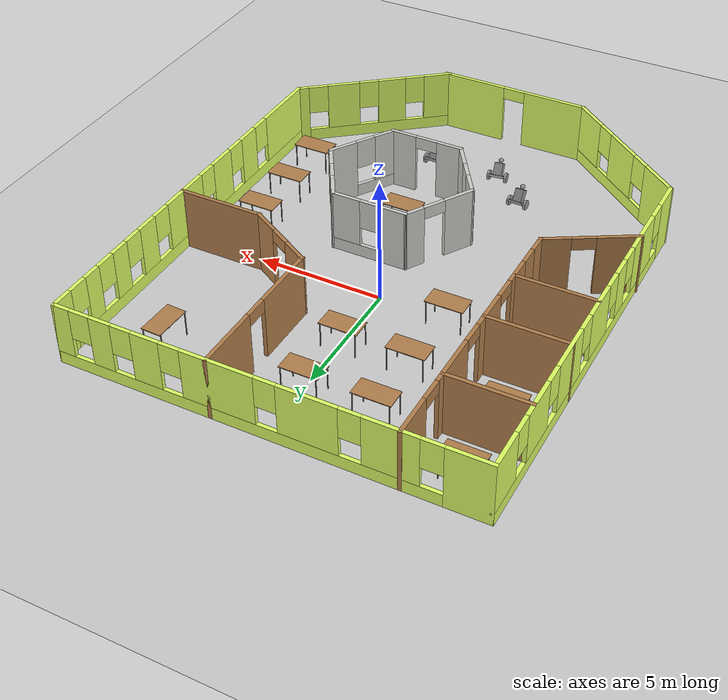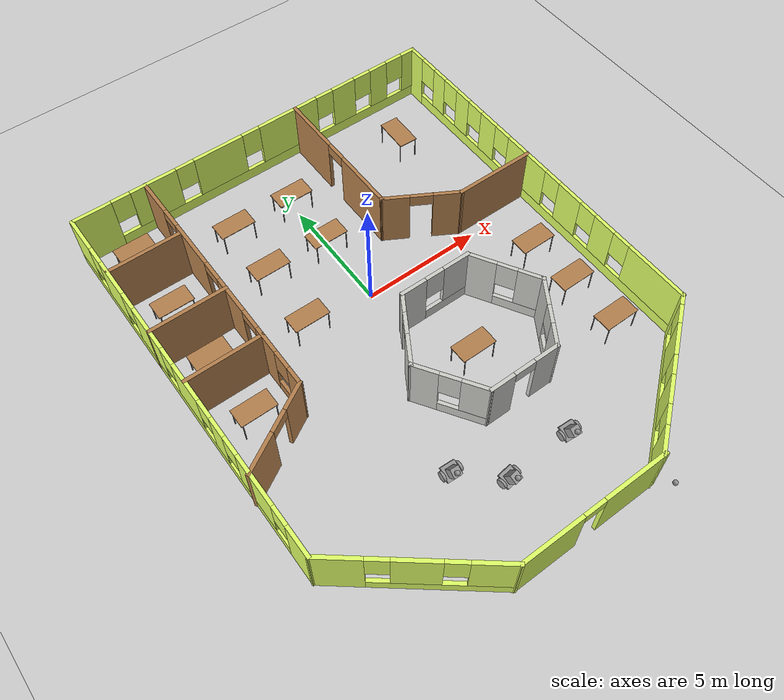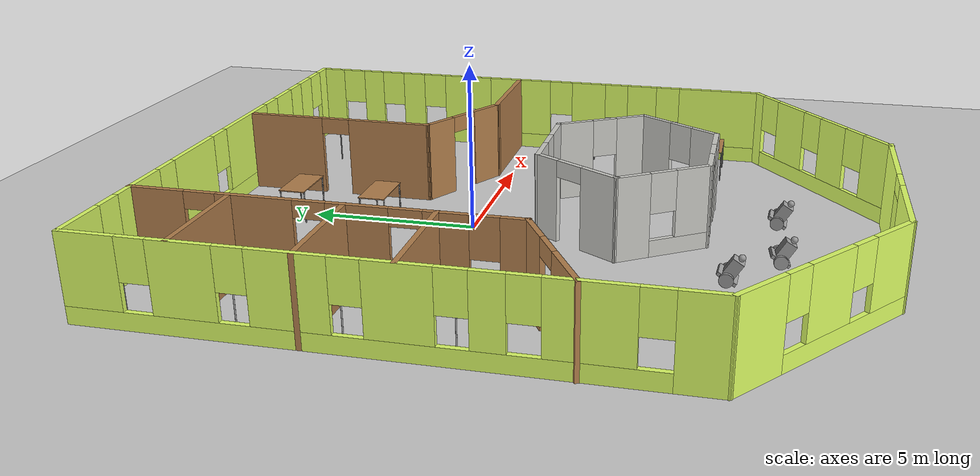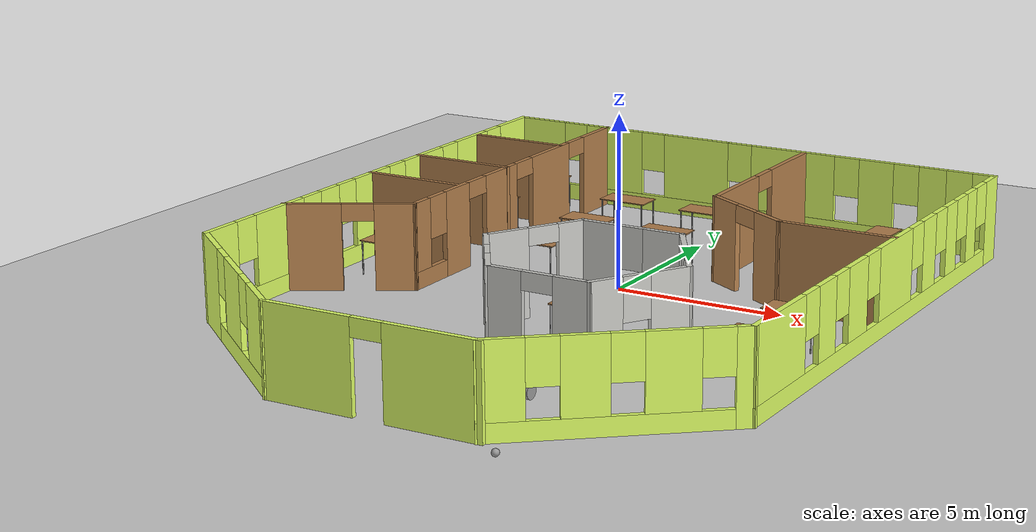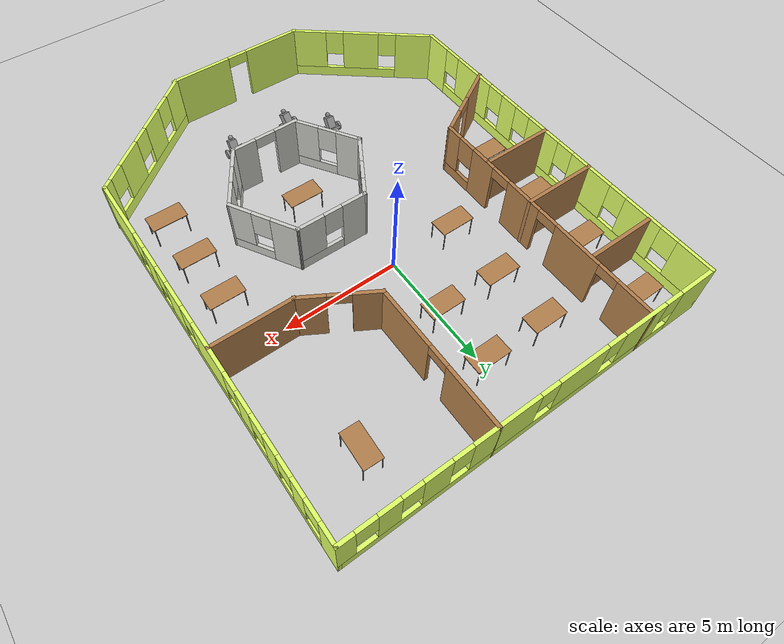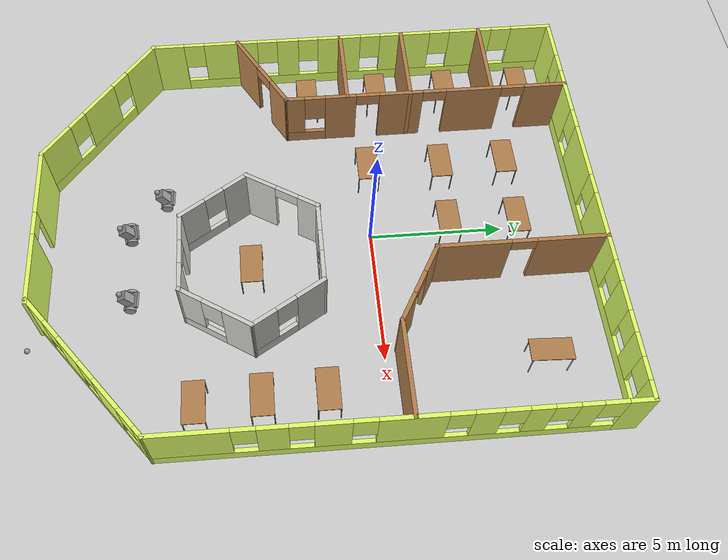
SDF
<sdf version="1.6">
 <world name="default">
  <plugin name="hello" filename="libhello.so"/>
  <light name="sun" type="directional">
   <pose>0 0 10 0 -0 0</pose>
   <diffuse>0.8 0.8 0.8 1</diffuse>
   <specular>0.2 0.2 0.2 1</specular>
   <attenuation>
    <range>1000</range>
    <constant>0.9</constant>
    <linear>0.01</linear>
    <quadratic>0.001</quadratic>
   </attenuation>
   <direction>-0.5 0.1 -0.9</direction>
  </light>
  <model name="ground_plane">
   <static>1</static>
   <link name="link">
    <collision name="collision">
     <geometry><plane><normal>0 0 1</normal><size>100 100</size></plane></geometry>
     <surface>
      <contact><collide_bitmask>65535</collide_bitmask></contact>
      <friction><ode><mu>100</mu><mu2>50</mu2></ode></friction>
     </surface>
    </collision>
    <visual name="visual">
     <cast_shadows>0</cast_shadows>
     <geometry><plane><normal>0 0 1</normal><size>100 100</size></plane></geometry>
     <material>
      <script><uri>file://media/materials/scripts/gazebo.material</uri><name>Gazebo/Grey</name></script>
     </material>
    </visual>
   </link>
  </model>
  <gravity>0 0 -9.8</gravity>
  <magnetic_field>6e-06 2.3e-05 -4.2e-05</magnetic_field>
  <atmosphere type="adiabatic"/>
  <physics name="default_physics" default="0" type="ode">
   <max_step_size>0.001</max_step_size>
   <real_time_factor>1</real_time_factor>
   <real_time_update_rate>1000</real_time_update_rate>
  </physics>
  <scene><ambient>0.4 0.4 0.4 1</ambient><background>0.7 0.7 0.7 1</background><shadows>1</shadows></scene>
  <spherical_coordinates>
   <surface_model>EARTH_WGS84</surface_model>
   <latitude_deg>0</latitude_deg>
   <longitude_deg>0</longitude_deg>
   <elevation>0</elevation>
   <heading_deg>0</heading_deg>
  </spherical_coordinates>
  <model name="myBuilding">
   <pose>-0.01524 -2.0117 0 0 -0 0</pose>
   <link name="Wall_1">
    <pose>-7.98476 2.0117 0 0 -0 1.5708</pose>
    <visual name="Wall_1_Visual_0">
     <pose>-7.43035 0 1.25 0 -0 0</pose>
     <geometry><box><size>1.2893 0.15 2.5</size></box></geometry>
     <material>
      <script><uri>file://media/materials/scripts/gazebo.material</uri><name>Gazebo/Grey</name></script>
      <ambient>0.870588 1 0.4 1</ambient>
     </material>
     <meta><layer>0</layer></meta>
    </visual>
    <collision name="Wall_1_Collision_0">
     <geometry><box><size>1.2893 0.15 2.5</size></box></geometry>
     <pose>-7.43035 0 1.25 0 -0 0</pose>
    </collision>
    <visual name="Wall_1_Visual_1">
     <pose>0.64465 0 0.25 0 -0 0</pose>
     <geometry><box><size>14.8607 0.15 0.5</size></box></geometry>
     <material>
      <script><uri>file://media/materials/scripts/gazebo.material</uri><name>Gazebo/Grey</name></script>
      <ambient>0.870588 1 0.4 1</ambient>
     </material>
     <meta><layer>0</layer></meta>
    </visual>
    <collision name="Wall_1_Collision_1">
     <geometry><box><size>14.8607 0.15 0.5</size></box></geometry>
     <pose>0.64465 0 0.25 0 -0 0</pose>
    </collision>
    <visual name="Wall_1_Visual_2">
     <pose>-4.91735 0 1.5 0 -0 0</pose>
     <geometry><box><size>2.13671 0.15 2</size></box></geometry>
     <material>
      <script><uri>file://media/materials/scripts/gazebo.material</uri><name>Gazebo/Grey</name></script>
      <ambient>0.870588 1 0.4 1</ambient>
     </material>
     <meta><layer>0</layer></meta>
    </visual>
    <collision name="Wall_1_Collision_2">
     <geometry><box><size>2.13671 0.15 2</size></box></geometry>
     <pose>-4.91735 0 1.5 0 -0 0</pose>
    </collision>
    <visual name="Wall_1_Visual_3">
     <pose>-2.61971 0 1.5 0 -0 0</pose>
     <geometry><box><size>0.858577 0.15 2</size></box></geometry>
     <material>
      <script><uri>file://media/materials/scripts/gazebo.material</uri><name>Gazebo/Grey</name></script>
      <ambient>0.870588 1 0.4 1</ambient>
     </material>
     <meta><layer>0</layer></meta>
    </visual>
    <collision name="Wall_1_Collision_3">
     <geometry><box><size>0.858577 0.15 2</size></box></geometry>
     <pose>-2.61971 0 1.5 0 -0 0</pose>
    </collision>
    <visual name="Wall_1_Visual_4">
     <pose>-0.533107 0 1.5 0 -0 0</pose>
     <geometry><box><size>1.71462 0.15 2</size></box></geometry>
     <material>
      <script><uri>file://media/materials/scripts/gazebo.material</uri><name>Gazebo/Grey</name></script>
      <ambient>0.870588 1 0.4 1</ambient>
     </material>
     <meta><layer>0</layer></meta>
    </visual>
    <collision name="Wall_1_Collision_4">
     <geometry><box><size>1.71462 0.15 2</size></box></geometry>
     <pose>-0.533107 0 1.5 0 -0 0</pose>
    </collision>
    <visual name="Wall_1_Visual_5">
     <pose>2.14202 0 1.5 0 -0 0</pose>
     <geometry><box><size>2.03563 0.15 2</size></box></geometry>
     <material>
      <script><uri>file://media/materials/scripts/gazebo.material</uri><name>Gazebo/Grey</name></script>
      <ambient>0.870588 1 0.4 1</ambient>
     </material>
     <meta><layer>0</layer></meta>
    </visual>
    <collision name="Wall_1_Collision_5">
     <geometry><box><size>2.03563 0.15 2</size></box></geometry>
     <pose>2.14202 0 1.5 0 -0 0</pose>
    </collision>
    <visual name="Wall_1_Visual_6">
     <pose>4.81656 0 1.5 0 -0 0</pose>
     <geometry><box><size>1.71345 0.15 2</size></box></geometry>
     <material>
      <script><uri>file://media/materials/scripts/gazebo.material</uri><name>Gazebo/Grey</name></script>
      <ambient>0.870588 1 0.4 1</ambient>
     </material>
     <meta><layer>0</layer></meta>
    </visual>
    <collision name="Wall_1_Collision_6">
     <geometry><box><size>1.71345 0.15 2</size></box></geometry>
     <pose>4.81656 0 1.5 0 -0 0</pose>
    </collision>
    <visual name="Wall_1_Visual_7">
     <pose>7.27414 0 1.5 0 -0 0</pose>
     <geometry><box><size>1.60171 0.15 2</size></box></geometry>
     <material>
      <script><uri>file://media/materials/scripts/gazebo.material</uri><name>Gazebo/Grey</name></script>
      <ambient>0.870588 1 0.4 1</ambient>
     </material>
     <meta><layer>0</layer></meta>
    </visual>
    <collision name="Wall_1_Collision_7">
     <geometry><box><size>1.60171 0.15 2</size></box></geometry>
     <pose>7.27414 0 1.5 0 -0 0</pose>
    </collision>
    <visual name="Wall_1_Visual_8">
     <pose>-6.3857 0 1.9 0 -0 0</pose>
     <geometry><box><size>0.8 0.15 1.2</size></box></geometry>
     <material>
      <script><uri>file://media/materials/scripts/gazebo.material</uri><name>Gazebo/Grey</name></script>
      <ambient>0.870588 1 0.4 1</ambient>
     </material>
     <meta><layer>0</layer></meta>
    </visual>
    <collision name="Wall_1_Collision_8">
     <geometry><box><size>0.8 0.15 1.2</size></box></geometry>
     <pose>-6.3857 0 1.9 0 -0 0</pose>
    </collision>
    <visual name="Wall_1_Visual_9">
     <pose>-3.44899 0 1.9 0 -0 0</pose>
     <geometry><box><size>0.8 0.15 1.2</size></box></geometry>
     <material>
      <script><uri>file://media/materials/scripts/gazebo.material</uri><name>Gazebo/Grey</name></script>
      <ambient>0.870588 1 0.4 1</ambient>
     </material>
     <meta><layer>0</layer></meta>
    </visual>
    <collision name="Wall_1_Collision_9">
     <geometry><box><size>0.8 0.15 1.2</size></box></geometry>
     <pose>-3.44899 0 1.9 0 -0 0</pose>
    </collision>
    <visual name="Wall_1_Visual_10">
     <pose>-1.79042 0 1.9 0 -0 0</pose>
     <geometry><box><size>0.8 0.15 1.2</size></box></geometry>
     <material>
      <script><uri>file://media/materials/scripts/gazebo.material</uri><name>Gazebo/Grey</name></script>
      <ambient>0.870588 1 0.4 1</ambient>
     </material>
     <meta><layer>0</layer></meta>
    </visual>
    <collision name="Wall_1_Collision_10">
     <geometry><box><size>0.8 0.15 1.2</size></box></geometry>
     <pose>-1.79042 0 1.9 0 -0 0</pose>
    </collision>
    <visual name="Wall_1_Visual_11">
     <pose>0.724202 0 1.9 0 -0 0</pose>
     <geometry><box><size>0.8 0.15 1.2</size></box></geometry>
     <material>
      <script><uri>file://media/materials/scripts/gazebo.material</uri><name>Gazebo/Grey</name></script>
      <ambient>0.870588 1 0.4 1</ambient>
     </material>
     <meta><layer>0</layer></meta>
    </visual>
    <collision name="Wall_1_Collision_11">
     <geometry><box><size>0.8 0.15 1.2</size></box></geometry>
     <pose>0.724202 0 1.9 0 -0 0</pose>
    </collision>
    <visual name="Wall_1_Visual_12">
     <pose>3.55983 0 1.9 0 -0 0</pose>
     <geometry><box><size>0.8 0.15 1.2</size></box></geometry>
     <material>
      <script><uri>file://media/materials/scripts/gazebo.material</uri><name>Gazebo/Grey</name></script>
      <ambient>0.870588 1 0.4 1</ambient>
     </material>
     <meta><layer>0</layer></meta>
    </visual>
    <collision name="Wall_1_Collision_12">
     <geometry><box><size>0.8 0.15 1.2</size></box></geometry>
     <pose>3.55983 0 1.9 0 -0 0</pose>
    </collision>
    <visual name="Wall_1_Visual_13">
     <pose>6.07329 0 1.9 0 -0 0</pose>
     <geometry><box><size>0.8 0.15 1.2</size></box></geometry>
     <material>
      <script><uri>file://media/materials/scripts/gazebo.material</uri><name>Gazebo/Grey</name></script>
      <ambient>0.870588 1 0.4 1</ambient>
     </material>
     <meta><layer>0</layer></meta>
    </visual>
    <collision name="Wall_1_Collision_13">
     <geometry><box><size>0.8 0.15 1.2</size></box></geometry>
     <pose>6.07329 0 1.9 0 -0 0</pose>
    </collision>
   </link>
   <link name="Wall_10">
    <pose>5.51524 -7.9883 0 0 0 -2.46685</pose>
    <visual name="Wall_10_Visual_0">
     <pose>-3.02719 0 1.25 0 -0 0</pose>
     <geometry><box><size>0.498745 0.15 2.5</size></box></geometry>
     <material>
      <script><uri>file://media/materials/scripts/gazebo.material</uri><name>Gazebo/Grey</name></script>
      <ambient>0.870588 1 0.4 1</ambient>
     </material>
     <meta><layer>0</layer></meta>
    </visual>
    <collision name="Wall_10_Collision_0">
     <geometry><box><size>0.498745 0.15 2.5</size></box></geometry>
     <pose>-3.02719 0 1.25 0 -0 0</pose>
    </collision>
    <visual name="Wall_10_Visual_1">
     <pose>0.249372 0 0.25 0 -0 0</pose>
     <geometry><box><size>6.05438 0.15 0.5</size></box></geometry>
     <material>
      <script><uri>file://media/materials/scripts/gazebo.material</uri><name>Gazebo/Grey</name></script>
      <ambient>0.870588 1 0.4 1</ambient>
     </material>
     <meta><layer>0</layer></meta>
    </visual>
    <collision name="Wall_10_Collision_1">
     <geometry><box><size>6.05438 0.15 0.5</size></box></geometry>
     <pose>0.249372 0 0.25 0 -0 0</pose>
    </collision>
    <visual name="Wall_10_Visual_2">
     <pose>-1.31246 0 1.5 0 -0 0</pose>
     <geometry><box><size>1.33072 0.15 2</size></box></geometry>
     <material>
      <script><uri>file://media/materials/scripts/gazebo.material</uri><name>Gazebo/Grey</name></script>
      <ambient>0.870588 1 0.4 1</ambient>
     </material>
     <meta><layer>0</layer></meta>
    </visual>
    <collision name="Wall_10_Collision_2">
     <geometry><box><size>1.33072 0.15 2</size></box></geometry>
     <pose>-1.31246 0 1.5 0 -0 0</pose>
    </collision>
    <visual name="Wall_10_Visual_3">
     <pose>0.732264 0 1.5 0 -0 0</pose>
     <geometry><box><size>1.15873 0.15 2</size></box></geometry>
     <material>
      <script><uri>file://media/materials/scripts/gazebo.material</uri><name>Gazebo/Grey</name></script>
      <ambient>0.870588 1 0.4 1</ambient>
     </material>
     <meta><layer>0</layer></meta>
    </visual>
    <collision name="Wall_10_Collision_3">
     <geometry><box><size>1.15873 0.15 2</size></box></geometry>
     <pose>0.732264 0 1.5 0 -0 0</pose>
    </collision>
    <visual name="Wall_10_Visual_4">
     <pose>2.6941 0 1.5 0 -0 0</pose>
     <geometry><box><size>1.16493 0.15 2</size></box></geometry>
     <material>
      <script><uri>file://media/materials/scripts/gazebo.material</uri><name>Gazebo/Grey</name></script>
      <ambient>0.870588 1 0.4 1</ambient>
     </material>
     <meta><layer>0</layer></meta>
    </visual>
    <collision name="Wall_10_Collision_4">
     <geometry><box><size>1.16493 0.15 2</size></box></geometry>
     <pose>2.6941 0 1.5 0 -0 0</pose>
    </collision>
    <visual name="Wall_10_Visual_5">
     <pose>-2.37782 0 1.9 0 -0 0</pose>
     <geometry><box><size>0.8 0.15 1.2</size></box></geometry>
     <material>
      <script><uri>file://media/materials/scripts/gazebo.material</uri><name>Gazebo/Grey</name></script>
      <ambient>0.870588 1 0.4 1</ambient>
     </material>
     <meta><layer>0</layer></meta>
    </visual>
    <collision name="Wall_10_Collision_5">
     <geometry><box><size>0.8 0.15 1.2</size></box></geometry>
     <pose>-2.37782 0 1.9 0 -0 0</pose>
    </collision>
    <visual name="Wall_10_Visual_6">
     <pose>-0.247101 0 1.9 0 -0 0</pose>
     <geometry><box><size>0.8 0.15 1.2</size></box></geometry>
     <material>
      <script><uri>file://media/materials/scripts/gazebo.material</uri><name>Gazebo/Grey</name></script>
      <ambient>0.870588 1 0.4 1</ambient>
     </material>
     <meta><layer>0</layer></meta>
    </visual>
    <collision name="Wall_10_Collision_6">
     <geometry><box><size>0.8 0.15 1.2</size></box></geometry>
     <pose>-0.247101 0 1.9 0 -0 0</pose>
    </collision>
    <visual name="Wall_10_Visual_7">
     <pose>1.71163 0 1.9 0 -0 0</pose>
     <geometry><box><size>0.8 0.15 1.2</size></box></geometry>
     <material>
      <script><uri>file://media/materials/scripts/gazebo.material</uri><name>Gazebo/Grey</name></script>
      <ambient>0.870588 1 0.4 1</ambient>
     </material>
     <meta><layer>0</layer></meta>
    </visual>
    <collision name="Wall_10_Collision_7">
     <geometry><box><size>0.8 0.15 1.2</size></box></geometry>
     <pose>1.71163 0 1.9 0 -0 0</pose>
    </collision>
   </link>
   <link name="Wall_12">
    <pose>0.065237 -9.9883 0 0 -0 0</pose>
    <visual name="Wall_12_Visual_0">
     <pose>-1.8125 0 1.25 0 -0 0</pose>
     <geometry><box><size>2.625 0.15 2.5</size></box></geometry>
     <material>
      <script><uri>file://media/materials/scripts/gazebo.material</uri><name>Gazebo/Grey</name></script>
      <ambient>0.870588 1 0.4 1</ambient>
     </material>
     <meta><layer>0</layer></meta>
    </visual>
    <collision name="Wall_12_Collision_0">
     <geometry><box><size>2.625 0.15 2.5</size></box></geometry>
     <pose>-1.8125 0 1.25 0 -0 0</pose>
    </collision>
    <visual name="Wall_12_Visual_1">
     <pose>1.7625 0 1.25 0 -0 0</pose>
     <geometry><box><size>2.725 0.15 2.5</size></box></geometry>
     <material>
      <script><uri>file://media/materials/scripts/gazebo.material</uri><name>Gazebo/Grey</name></script>
      <ambient>0.870588 1 0.4 1</ambient>
     </material>
     <meta><layer>0</layer></meta>
    </visual>
    <collision name="Wall_12_Collision_1">
     <geometry><box><size>2.725 0.15 2.5</size></box></geometry>
     <pose>1.7625 0 1.25 0 -0 0</pose>
    </collision>
    <visual name="Wall_12_Visual_2">
     <pose>-0.05 0 2.25 0 -0 0</pose>
     <geometry><box><size>0.9 0.15 0.5</size></box></geometry>
     <material>
      <script><uri>file://media/materials/scripts/gazebo.material</uri><name>Gazebo/Grey</name></script>
      <ambient>0.870588 1 0.4 1</ambient>
     </material>
     <meta><layer>0</layer></meta>
    </visual>
    <collision name="Wall_12_Collision_2">
     <geometry><box><size>0.9 0.15 0.5</size></box></geometry>
     <pose>-0.05 0 2.25 0 -0 0</pose>
    </collision>
   </link>
   <link name="Wall_14">
    <pose>2.01524 7.0117 0 0 0 -1.5708</pose>
    <visual name="Wall_14_Visual_0">
     <pose>-1.79003 0 1.25 0 -0 0</pose>
     <geometry><box><size>2.56994 0.15 2.5</size></box></geometry>
     <material>
      <script><uri>file://media/materials/scripts/gazebo.material</uri><name>Gazebo/Wood</name></script>
      <ambient>1 0.976471 0.866667 1</ambient>
     </material>
     <meta><layer>0</layer></meta>
    </visual>
    <collision name="Wall_14_Collision_0">
     <geometry><box><size>2.56994 0.15 2.5</size></box></geometry>
     <pose>-1.79003 0 1.25 0 -0 0</pose>
    </collision>
    <visual name="Wall_14_Visual_1">
     <pose>1.73497 0 1.25 0 -0 0</pose>
     <geometry><box><size>2.68006 0.15 2.5</size></box></geometry>
     <material>
      <script><uri>file://media/materials/scripts/gazebo.material</uri><name>Gazebo/Wood</name></script>
      <ambient>1 0.976471 0.866667 1</ambient>
     </material>
     <meta><layer>0</layer></meta>
    </visual>
    <collision name="Wall_14_Collision_1">
     <geometry><box><size>2.68006 0.15 2.5</size></box></geometry>
     <pose>1.73497 0 1.25 0 -0 0</pose>
    </collision>
    <visual name="Wall_14_Visual_2">
     <pose>-0.055061 0 2.25 0 -0 0</pose>
     <geometry><box><size>0.9 0.15 0.5</size></box></geometry>
     <material>
      <script><uri>file://media/materials/scripts/gazebo.material</uri><name>Gazebo/Wood</name></script>
      <ambient>1 0.976471 0.866667 1</ambient>
     </material>
     <meta><layer>0</layer></meta>
    </visual>
    <collision name="Wall_14_Collision_2">
     <geometry><box><size>0.9 0.15 0.5</size></box></geometry>
     <pose>-0.055061 0 2.25 0 -0 0</pose>
    </collision>
   </link>
   <link name="Wall_16">
    <pose>3.35774 3.2367 0 0 0 -0.523547</pose>
    <visual name="Wall_16_Visual_0">
     <pose>-1.0429 0 1.25 0 -0 0</pose>
     <geometry><box><size>1.1642 0.15 2.5</size></box></geometry>
     <material>
      <script><uri>file://media/materials/scripts/gazebo.material</uri><name>Gazebo/Wood</name></script>
      <ambient>1 0.976471 0.866667 1</ambient>
     </material>
     <meta><layer>0</layer></meta>
    </visual>
    <collision name="Wall_16_Collision_0">
     <geometry><box><size>1.1642 0.15 2.5</size></box></geometry>
     <pose>-1.0429 0 1.25 0 -0 0</pose>
    </collision>
    <visual name="Wall_16_Visual_1">
     <pose>1.0321 0 1.25 0 -0 0</pose>
     <geometry><box><size>1.1858 0.15 2.5</size></box></geometry>
     <material>
      <script><uri>file://media/materials/scripts/gazebo.material</uri><name>Gazebo/Wood</name></script>
      <ambient>1 0.976471 0.866667 1</ambient>
     </material>
     <meta><layer>0</layer></meta>
    </visual>
    <collision name="Wall_16_Collision_1">
     <geometry><box><size>1.1858 0.15 2.5</size></box></geometry>
     <pose>1.0321 0 1.25 0 -0 0</pose>
    </collision>
    <visual name="Wall_16_Visual_2">
     <pose>-0.010799 0 2.25 0 -0 0</pose>
     <geometry><box><size>0.9 0.15 0.5</size></box></geometry>
     <material>
      <script><uri>file://media/materials/scripts/gazebo.material</uri><name>Gazebo/Wood</name></script>
      <ambient>1 0.976471 0.866667 1</ambient>
     </material>
     <meta><layer>0</layer></meta>
    </visual>
    <collision name="Wall_16_Collision_2">
     <geometry><box><size>0.9 0.15 0.5</size></box></geometry>
     <pose>-0.010799 0 2.25 0 -0 0</pose>
    </collision>
   </link>
   <link name="Wall_18">
    <collision name="Wall_18_Collision">
     <geometry><box><size>3.465 0.15 2.5</size></box></geometry>
     <pose>0 0 1.25 0 -0 0</pose>
    </collision>
    <visual name="Wall_18_Visual">
     <pose>0 0 1.25 0 -0 0</pose>
     <geometry><box><size>3.465 0.15 2.5</size></box></geometry>
     <material>
      <script><uri>file://media/materials/scripts/gazebo.material</uri><name>Gazebo/Wood</name></script>
      <ambient>1 0.976471 0.866667 1</ambient>
     </material>
     <meta><layer>0</layer></meta>
    </visual>
    <pose>6.35774 2.4617 0 0 -0 0</pose>
   </link>
   <link name="Wall_21">
    <pose>-4.90051 4.59371 0 0 0 -1.5708</pose>
    <visual name="Wall_21_Visual_0">
     <pose>-4.67112 0 1.25 0 -0 0</pose>
     <geometry><box><size>1.65776 0.15 2.5</size></box></geometry>
     <material>
      <script><uri>file://media/materials/scripts/gazebo.material</uri><name>Gazebo/Wood</name></script>
      <ambient>1 0.976471 0.866667 1</ambient>
     </material>
     <meta><layer>0</layer></meta>
    </visual>
    <collision name="Wall_21_Collision_0">
     <geometry><box><size>1.65776 0.15 2.5</size></box></geometry>
     <pose>-4.67112 0 1.25 0 -0 0</pose>
    </collision>
    <visual name="Wall_21_Visual_1">
     <pose>-1.86272 0 1.25 0 -0 0</pose>
     <geometry><box><size>2.15902 0.15 2.5</size></box></geometry>
     <material>
      <script><uri>file://media/materials/scripts/gazebo.material</uri><name>Gazebo/Wood</name></script>
      <ambient>1 0.976471 0.866667 1</ambient>
     </material>
     <meta><layer>0</layer></meta>
    </visual>
    <collision name="Wall_21_Collision_1">
     <geometry><box><size>2.15902 0.15 2.5</size></box></geometry>
     <pose>-1.86272 0 1.25 0 -0 0</pose>
    </collision>
    <visual name="Wall_21_Visual_2">
     <pose>0.966873 0 1.25 0 -0 0</pose>
     <geometry><box><size>1.70017 0.15 2.5</size></box></geometry>
     <material>
      <script><uri>file://media/materials/scripts/gazebo.material</uri><name>Gazebo/Wood</name></script>
      <ambient>1 0.976471 0.866667 1</ambient>
     </material>
     <meta><layer>0</layer></meta>
    </visual>
    <collision name="Wall_21_Collision_2">
     <geometry><box><size>1.70017 0.15 2.5</size></box></geometry>
     <pose>0.966873 0 1.25 0 -0 0</pose>
    </collision>
    <visual name="Wall_21_Visual_3">
     <pose>3.31748 0 1.25 0 -0 0</pose>
     <geometry><box><size>1.20104 0.15 2.5</size></box></geometry>
     <material>
      <script><uri>file://media/materials/scripts/gazebo.material</uri><name>Gazebo/Wood</name></script>
      <ambient>1 0.976471 0.866667 1</ambient>
     </material>
     <meta><layer>0</layer></meta>
    </visual>
    <collision name="Wall_21_Collision_3">
     <geometry><box><size>1.20104 0.15 2.5</size></box></geometry>
     <pose>3.31748 0 1.25 0 -0 0</pose>
    </collision>
    <visual name="Wall_21_Visual_4">
     <pose>4.709 0 0.25 0 -0 0</pose>
     <geometry><box><size>1.582 0.15 0.5</size></box></geometry>
     <material>
      <script><uri>file://media/materials/scripts/gazebo.material</uri><name>Gazebo/Wood</name></script>
      <ambient>1 0.976471 0.866667 1</ambient>
     </material>
     <meta><layer>0</layer></meta>
    </visual>
    <collision name="Wall_21_Collision_4">
     <geometry><box><size>1.582 0.15 0.5</size></box></geometry>
     <pose>4.709 0 0.25 0 -0 0</pose>
    </collision>
    <visual name="Wall_21_Visual_5">
     <pose>5.109 0 1.5 0 -0 0</pose>
     <geometry><box><size>0.782004 0.15 2</size></box></geometry>
     <material>
      <script><uri>file://media/materials/scripts/gazebo.material</uri><name>Gazebo/Wood</name></script>
      <ambient>1 0.976471 0.866667 1</ambient>
     </material>
     <meta><layer>0</layer></meta>
    </visual>
    <collision name="Wall_21_Collision_5">
     <geometry><box><size>0.782004 0.15 2</size></box></geometry>
     <pose>5.109 0 1.5 0 -0 0</pose>
    </collision>
    <visual name="Wall_21_Visual_6">
     <pose>4.318 0 1.9 0 -0 0</pose>
     <geometry><box><size>0.8 0.15 1.2</size></box></geometry>
     <material>
      <script><uri>file://media/materials/scripts/gazebo.material</uri><name>Gazebo/Wood</name></script>
      <ambient>1 0.976471 0.866667 1</ambient>
     </material>
     <meta><layer>0</layer></meta>
    </visual>
    <collision name="Wall_21_Collision_6">
     <geometry><box><size>0.8 0.15 1.2</size></box></geometry>
     <pose>4.318 0 1.9 0 -0 0</pose>
    </collision>
    <visual name="Wall_21_Visual_7">
     <pose>-3.39223 0 2.25 0 -0 0</pose>
     <geometry><box><size>0.9 0.15 0.5</size></box></geometry>
     <material>
      <script><uri>file://media/materials/scripts/gazebo.material</uri><name>Gazebo/Wood</name></script>
      <ambient>1 0.976471 0.866667 1</ambient>
     </material>
     <meta><layer>0</layer></meta>
    </visual>
    <collision name="Wall_21_Collision_7">
     <geometry><box><size>0.9 0.15 0.5</size></box></geometry>
     <pose>-3.39223 0 2.25 0 -0 0</pose>
    </collision>
    <visual name="Wall_21_Visual_8">
     <pose>-0.333212 0 2.25 0 -0 0</pose>
     <geometry><box><size>0.9 0.15 0.5</size></box></geometry>
     <material>
      <script><uri>file://media/materials/scripts/gazebo.material</uri><name>Gazebo/Wood</name></script>
      <ambient>1 0.976471 0.866667 1</ambient>
     </material>
     <meta><layer>0</layer></meta>
    </visual>
    <collision name="Wall_21_Collision_8">
     <geometry><box><size>0.9 0.15 0.5</size></box></geometry>
     <pose>-0.333212 0 2.25 0 -0 0</pose>
    </collision>
    <visual name="Wall_21_Visual_9">
     <pose>2.26696 0 2.25 0 -0 0</pose>
     <geometry><box><size>0.9 0.15 0.5</size></box></geometry>
     <material>
      <script><uri>file://media/materials/scripts/gazebo.material</uri><name>Gazebo/Wood</name></script>
      <ambient>1 0.976471 0.866667 1</ambient>
     </material>
     <meta><layer>0</layer></meta>
    </visual>
    <collision name="Wall_21_Collision_9">
     <geometry><box><size>0.9 0.15 0.5</size></box></geometry>
     <pose>2.26696 0 2.25 0 -0 0</pose>
    </collision>
   </link>
   <link name="Wall_22">
    <pose>-6.45936 -1.73129 0 0 0 -2.61799</pose>
    <visual name="Wall_22_Visual_0">
     <pose>-1.28514 0 1.25 0 -0 0</pose>
     <geometry><box><size>1.17972 0.15 2.5</size></box></geometry>
     <material>
      <script><uri>file://media/materials/scripts/gazebo.material</uri><name>Gazebo/Wood</name></script>
      <ambient>1 0.976471 0.866667 1</ambient>
     </material>
     <meta><layer>0</layer></meta>
    </visual>
    <collision name="Wall_22_Collision_0">
     <geometry><box><size>1.17972 0.15 2.5</size></box></geometry>
     <pose>-1.28514 0 1.25 0 -0 0</pose>
    </collision>
    <visual name="Wall_22_Visual_1">
     <pose>1.03986 0 1.25 0 -0 0</pose>
     <geometry><box><size>1.67028 0.15 2.5</size></box></geometry>
     <material>
      <script><uri>file://media/materials/scripts/gazebo.material</uri><name>Gazebo/Wood</name></script>
      <ambient>1 0.976471 0.866667 1</ambient>
     </material>
     <meta><layer>0</layer></meta>
    </visual>
    <collision name="Wall_22_Collision_1">
     <geometry><box><size>1.67028 0.15 2.5</size></box></geometry>
     <pose>1.03986 0 1.25 0 -0 0</pose>
    </collision>
    <visual name="Wall_22_Visual_2">
     <pose>-0.24528 0 2.25 0 -0 0</pose>
     <geometry><box><size>0.9 0.15 0.5</size></box></geometry>
     <material>
      <script><uri>file://media/materials/scripts/gazebo.material</uri><name>Gazebo/Wood</name></script>
      <ambient>1 0.976471 0.866667 1</ambient>
     </material>
     <meta><layer>0</layer></meta>
    </visual>
    <collision name="Wall_22_Collision_2">
     <geometry><box><size>0.9 0.15 0.5</size></box></geometry>
     <pose>-0.24528 0 2.25 0 -0 0</pose>
    </collision>
   </link>
   <link name="Wall_29">
    <collision name="Wall_29_Collision">
     <geometry><box><size>3.23933 0.15 2.5</size></box></geometry>
     <pose>0 0 1.25 0 -0 0</pose>
    </collision>
    <visual name="Wall_29_Visual">
     <pose>0 0 1.25 0 -0 0</pose>
     <geometry><box><size>3.23933 0.15 2.5</size></box></geometry>
     <material>
      <script><uri>file://media/materials/scripts/gazebo.material</uri><name>Gazebo/Wood</name></script>
      <ambient>1 0.976471 0.866667 1</ambient>
     </material>
     <meta><layer>0</layer></meta>
    </visual>
    <pose>-6.44026 3.9777 0 0 -0 0</pose>
   </link>
   <link name="Wall_31">
    <collision name="Wall_31_Collision">
     <geometry><box><size>3.234 0.15 2.5</size></box></geometry>
     <pose>0 0 1.25 0 -0 0</pose>
    </collision>
    <visual name="Wall_31_Visual">
     <pose>0 0 1.25 0 -0 0</pose>
     <geometry><box><size>3.234 0.15 2.5</size></box></geometry>
     <material>
      <script><uri>file://media/materials/scripts/gazebo.material</uri><name>Gazebo/Wood</name></script>
      <ambient>1 0.976471 0.866667 1</ambient>
     </material>
     <meta><layer>0</layer></meta>
    </visual>
    <pose>-6.44276 7.1467 0 0 -0 0</pose>
   </link>
   <link name="Wall_35">
    <collision name="Wall_35_Collision">
     <geometry><box><size>3.22684 0.15 2.5</size></box></geometry>
     <pose>0 0 1.25 0 -0 0</pose>
    </collision>
    <visual name="Wall_35_Visual">
     <pose>0 0 1.25 0 -0 0</pose>
     <geometry><box><size>3.22684 0.15 2.5</size></box></geometry>
     <material>
      <script><uri>file://media/materials/scripts/gazebo.material</uri><name>Gazebo/Wood</name></script>
      <ambient>1 0.976471 0.866667 1</ambient>
     </material>
     <meta><layer>0</layer></meta>
    </visual>
    <pose>-6.44626 1.5187 0 0 -0 0</pose>
   </link>
   <link name="Wall_37">
    <pose>1.51524 0.011703 0 0 -0 0</pose>
    <visual name="Wall_37_Visual_0">
     <pose>-1.00885 0 1.25 0 -0 0</pose>
     <geometry><box><size>1.1323 0.15 2.5</size></box></geometry>
     <material>
      <script><uri>file://media/materials/scripts/gazebo.material</uri><name>Gazebo/CeilingTiled</name></script>
      <ambient>0.662745 0.929412 1 1</ambient>
     </material>
     <meta><layer>0</layer></meta>
    </visual>
    <collision name="Wall_37_Collision_0">
     <geometry><box><size>1.1323 0.15 2.5</size></box></geometry>
     <pose>-1.00885 0 1.25 0 -0 0</pose>
    </collision>
    <visual name="Wall_37_Visual_1">
     <pose>0.566152 0 0.25 0 -0 0</pose>
     <geometry><box><size>2.0177 0.15 0.5</size></box></geometry>
     <material>
      <script><uri>file://media/materials/scripts/gazebo.material</uri><name>Gazebo/CeilingTiled</name></script>
      <ambient>0.662745 0.929412 1 1</ambient>
     </material>
     <meta><layer>0</layer></meta>
    </visual>
    <collision name="Wall_37_Collision_1">
     <geometry><box><size>2.0177 0.15 0.5</size></box></geometry>
     <pose>0.566152 0 0.25 0 -0 0</pose>
    </collision>
    <visual name="Wall_37_Visual_2">
     <pose>0.966152 0 1.5 0 -0 0</pose>
     <geometry><box><size>1.2177 0.15 2</size></box></geometry>
     <material>
      <script><uri>file://media/materials/scripts/gazebo.material</uri><name>Gazebo/CeilingTiled</name></script>
      <ambient>0.662745 0.929412 1 1</ambient>
     </material>
     <meta><layer>0</layer></meta>
    </visual>
    <collision name="Wall_37_Collision_2">
     <geometry><box><size>1.2177 0.15 2</size></box></geometry>
     <pose>0.966152 0 1.5 0 -0 0</pose>
    </collision>
    <visual name="Wall_37_Visual_3">
     <pose>-0.042697 0 1.9 0 -0 0</pose>
     <geometry><box><size>0.8 0.15 1.2</size></box></geometry>
     <material>
      <script><uri>file://media/materials/scripts/gazebo.material</uri><name>Gazebo/CeilingTiled</name></script>
      <ambient>0.662745 0.929412 1 1</ambient>
     </material>
     <meta><layer>0</layer></meta>
    </visual>
    <collision name="Wall_37_Collision_3">
     <geometry><box><size>0.8 0.15 1.2</size></box></geometry>
     <pose>-0.042697 0 1.9 0 -0 0</pose>
    </collision>
   </link>
   <link name="Wall_4">
    <pose>0.015237 10.0117 0 0 -0 0</pose>
    <visual name="Wall_4_Visual_0">
     <pose>-7.22792 0 1.25 0 -0 0</pose>
     <geometry><box><size>1.69415 0.15 2.5</size></box></geometry>
     <material>
      <script><uri>file://media/materials/scripts/gazebo.material</uri><name>Gazebo/Grey</name></script>
      <ambient>0.870588 1 0.4 1</ambient>
     </material>
     <meta><layer>0</layer></meta>
    </visual>
    <collision name="Wall_4_Collision_0">
     <geometry><box><size>1.69415 0.15 2.5</size></box></geometry>
     <pose>-7.22792 0 1.25 0 -0 0</pose>
    </collision>
    <visual name="Wall_4_Visual_1">
     <pose>0.847076 0 0.25 0 -0 0</pose>
     <geometry><box><size>14.4558 0.15 0.5</size></box></geometry>
     <material>
      <script><uri>file://media/materials/scripts/gazebo.material</uri><name>Gazebo/Grey</name></script>
      <ambient>0.870588 1 0.4 1</ambient>
     </material>
     <meta><layer>0</layer></meta>
    </visual>
    <collision name="Wall_4_Collision_1">
     <geometry><box><size>14.4558 0.15 0.5</size></box></geometry>
     <pose>0.847076 0 0.25 0 -0 0</pose>
    </collision>
    <visual name="Wall_4_Visual_2">
     <pose>-4.58109 0 1.5 0 -0 0</pose>
     <geometry><box><size>1.99952 0.15 2</size></box></geometry>
     <material>
      <script><uri>file://media/materials/scripts/gazebo.material</uri><name>Gazebo/Grey</name></script>
      <ambient>0.870588 1 0.4 1</ambient>
     </material>
     <meta><layer>0</layer></meta>
    </visual>
    <collision name="Wall_4_Collision_2">
     <geometry><box><size>1.99952 0.15 2</size></box></geometry>
     <pose>-4.58109 0 1.5 0 -0 0</pose>
    </collision>
    <visual name="Wall_4_Visual_3">
     <pose>-1.6739 0 1.5 0 -0 0</pose>
     <geometry><box><size>2.21487 0.15 2</size></box></geometry>
     <material>
      <script><uri>file://media/materials/scripts/gazebo.material</uri><name>Gazebo/Grey</name></script>
      <ambient>0.870588 1 0.4 1</ambient>
     </material>
     <meta><layer>0</layer></meta>
    </visual>
    <collision name="Wall_4_Collision_3">
     <geometry><box><size>2.21487 0.15 2</size></box></geometry>
     <pose>-1.6739 0 1.5 0 -0 0</pose>
    </collision>
    <visual name="Wall_4_Visual_4">
     <pose>1.61784 0 1.5 0 -0 0</pose>
     <geometry><box><size>2.76862 0.15 2</size></box></geometry>
     <material>
      <script><uri>file://media/materials/scripts/gazebo.material</uri><name>Gazebo/Grey</name></script>
      <ambient>0.870588 1 0.4 1</ambient>
     </material>
     <meta><layer>0</layer></meta>
    </visual>
    <collision name="Wall_4_Collision_4">
     <geometry><box><size>2.76862 0.15 2</size></box></geometry>
     <pose>1.61784 0 1.5 0 -0 0</pose>
    </collision>
    <visual name="Wall_4_Visual_5">
     <pose>4.35583 0 1.5 0 -0 0</pose>
     <geometry><box><size>1.10736 0.15 2</size></box></geometry>
     <material>
      <script><uri>file://media/materials/scripts/gazebo.material</uri><name>Gazebo/Grey</name></script>
      <ambient>0.870588 1 0.4 1</ambient>
     </material>
     <meta><layer>0</layer></meta>
    </visual>
    <collision name="Wall_4_Collision_5">
     <geometry><box><size>1.10736 0.15 2</size></box></geometry>
     <pose>4.35583 0 1.5 0 -0 0</pose>
    </collision>
    <visual name="Wall_4_Visual_6">
     <pose>6.14014 0 1.5 0 -0 0</pose>
     <geometry><box><size>0.861253 0.15 2</size></box></geometry>
     <material>
      <script><uri>file://media/materials/scripts/gazebo.material</uri><name>Gazebo/Grey</name></script>
      <ambient>0.870588 1 0.4 1</ambient>
     </material>
     <meta><layer>0</layer></meta>
    </visual>
    <collision name="Wall_4_Collision_6">
     <geometry><box><size>0.861253 0.15 2</size></box></geometry>
     <pose>6.14014 0 1.5 0 -0 0</pose>
    </collision>
    <visual name="Wall_4_Visual_7">
     <pose>7.72288 0 1.5 0 -0 0</pose>
     <geometry><box><size>0.704231 0.15 2</size></box></geometry>
     <material>
      <script><uri>file://media/materials/scripts/gazebo.material</uri><name>Gazebo/Grey</name></script>
      <ambient>0.870588 1 0.4 1</ambient>
     </material>
     <meta><layer>0</layer></meta>
    </visual>
    <collision name="Wall_4_Collision_7">
     <geometry><box><size>0.704231 0.15 2</size></box></geometry>
     <pose>7.72288 0 1.5 0 -0 0</pose>
    </collision>
    <visual name="Wall_4_Visual_8">
     <pose>-5.98085 0 1.9 0 -0 0</pose>
     <geometry><box><size>0.8 0.15 1.2</size></box></geometry>
     <material>
      <script><uri>file://media/materials/scripts/gazebo.material</uri><name>Gazebo/Grey</name></script>
      <ambient>0.870588 1 0.4 1</ambient>
     </material>
     <meta><layer>0</layer></meta>
    </visual>
    <collision name="Wall_4_Collision_8">
     <geometry><box><size>0.8 0.15 1.2</size></box></geometry>
     <pose>-5.98085 0 1.9 0 -0 0</pose>
    </collision>
    <visual name="Wall_4_Visual_9">
     <pose>-3.18133 0 1.9 0 -0 0</pose>
     <geometry><box><size>0.8 0.15 1.2</size></box></geometry>
     <material>
      <script><uri>file://media/materials/scripts/gazebo.material</uri><name>Gazebo/Grey</name></script>
      <ambient>0.870588 1 0.4 1</ambient>
     </material>
     <meta><layer>0</layer></meta>
    </visual>
    <collision name="Wall_4_Collision_9">
     <geometry><box><size>0.8 0.15 1.2</size></box></geometry>
     <pose>-3.18133 0 1.9 0 -0 0</pose>
    </collision>
    <visual name="Wall_4_Visual_10">
     <pose>-0.166464 0 1.9 0 -0 0</pose>
     <geometry><box><size>0.8 0.15 1.2</size></box></geometry>
     <material>
      <script><uri>file://media/materials/scripts/gazebo.material</uri><name>Gazebo/Grey</name></script>
      <ambient>0.870588 1 0.4 1</ambient>
     </material>
     <meta><layer>0</layer></meta>
    </visual>
    <collision name="Wall_4_Collision_10">
     <geometry><box><size>0.8 0.15 1.2</size></box></geometry>
     <pose>-0.166464 0 1.9 0 -0 0</pose>
    </collision>
    <visual name="Wall_4_Visual_11">
     <pose>3.40215 0 1.9 0 -0 0</pose>
     <geometry><box><size>0.8 0.15 1.2</size></box></geometry>
     <material>
      <script><uri>file://media/materials/scripts/gazebo.material</uri><name>Gazebo/Grey</name></script>
      <ambient>0.870588 1 0.4 1</ambient>
     </material>
     <meta><layer>0</layer></meta>
    </visual>
    <collision name="Wall_4_Collision_11">
     <geometry><box><size>0.8 0.15 1.2</size></box></geometry>
     <pose>3.40215 0 1.9 0 -0 0</pose>
    </collision>
    <visual name="Wall_4_Visual_12">
     <pose>5.30952 0 1.9 0 -0 0</pose>
     <geometry><box><size>0.8 0.15 1.2</size></box></geometry>
     <material>
      <script><uri>file://media/materials/scripts/gazebo.material</uri><name>Gazebo/Grey</name></script>
      <ambient>0.870588 1 0.4 1</ambient>
     </material>
     <meta><layer>0</layer></meta>
    </visual>
    <collision name="Wall_4_Collision_12">
     <geometry><box><size>0.8 0.15 1.2</size></box></geometry>
     <pose>5.30952 0 1.9 0 -0 0</pose>
    </collision>
    <visual name="Wall_4_Visual_13">
     <pose>6.97077 0 1.9 0 -0 0</pose>
     <geometry><box><size>0.8 0.15 1.2</size></box></geometry>
     <material>
      <script><uri>file://media/materials/scripts/gazebo.material</uri><name>Gazebo/Grey</name></script>
      <ambient>0.870588 1 0.4 1</ambient>
     </material>
     <meta><layer>0</layer></meta>
    </visual>
    <collision name="Wall_4_Collision_13">
     <geometry><box><size>0.8 0.15 1.2</size></box></geometry>
     <pose>6.97077 0 1.9 0 -0 0</pose>
    </collision>
   </link>
   <link name="Wall_41">
    <pose>1.55274 -4.8883 0 0 -0 3.14159</pose>
    <visual name="Wall_41_Visual_0">
     <pose>-0.993879 0 1.25 0 -0 0</pose>
     <geometry><box><size>1.08724 0.15 2.5</size></box></geometry>
     <material>
      <script><uri>file://media/materials/scripts/gazebo.material</uri><name>Gazebo/CeilingTiled</name></script>
      <ambient>0.662745 0.929412 1 1</ambient>
     </material>
     <meta><layer>0</layer></meta>
    </visual>
    <collision name="Wall_41_Collision_0">
     <geometry><box><size>1.08724 0.15 2.5</size></box></geometry>
     <pose>-0.993879 0 1.25 0 -0 0</pose>
    </collision>
    <visual name="Wall_41_Visual_1">
     <pose>0.993621 0 1.25 0 -0 0</pose>
     <geometry><box><size>1.08776 0.15 2.5</size></box></geometry>
     <material>
      <script><uri>file://media/materials/scripts/gazebo.material</uri><name>Gazebo/CeilingTiled</name></script>
      <ambient>0.662745 0.929412 1 1</ambient>
     </material>
     <meta><layer>0</layer></meta>
    </visual>
    <collision name="Wall_41_Collision_1">
     <geometry><box><size>1.08776 0.15 2.5</size></box></geometry>
     <pose>0.993621 0 1.25 0 -0 0</pose>
    </collision>
    <visual name="Wall_41_Visual_2">
     <pose>-0.000257 0 2.25 0 -0 0</pose>
     <geometry><box><size>0.9 0.15 0.5</size></box></geometry>
     <material>
      <script><uri>file://media/materials/scripts/gazebo.material</uri><name>Gazebo/CeilingTiled</name></script>
      <ambient>0.662745 0.929412 1 1</ambient>
     </material>
     <meta><layer>0</layer></meta>
    </visual>
    <collision name="Wall_41_Collision_2">
     <geometry><box><size>0.9 0.15 0.5</size></box></geometry>
     <pose>-0.000257 0 2.25 0 -0 0</pose>
    </collision>
   </link>
   <link name="Wall_46">
    <pose>-0.734763 -1.2383 0 0 0 -2.11122</pose>
    <visual name="Wall_46_Visual_0">
     <pose>-1.10227 0 1.25 0 -0 0</pose>
     <geometry><box><size>0.860943 0.15 2.5</size></box></geometry>
     <material>
      <script><uri>file://media/materials/scripts/gazebo.material</uri><name>Gazebo/CeilingTiled</name></script>
      <ambient>0.662745 0.929412 1 1</ambient>
     </material>
     <meta><layer>0</layer></meta>
    </visual>
    <collision name="Wall_46_Collision_0">
     <geometry><box><size>0.860943 0.15 2.5</size></box></geometry>
     <pose>-1.10227 0 1.25 0 -0 0</pose>
    </collision>
    <visual name="Wall_46_Visual_1">
     <pose>0.880472 0 1.25 0 -0 0</pose>
     <geometry><box><size>1.30453 0.15 2.5</size></box></geometry>
     <material>
      <script><uri>file://media/materials/scripts/gazebo.material</uri><name>Gazebo/CeilingTiled</name></script>
      <ambient>0.662745 0.929412 1 1</ambient>
     </material>
     <meta><layer>0</layer></meta>
    </visual>
    <collision name="Wall_46_Collision_1">
     <geometry><box><size>1.30453 0.15 2.5</size></box></geometry>
     <pose>0.880472 0 1.25 0 -0 0</pose>
    </collision>
    <visual name="Wall_46_Visual_2">
     <pose>-0.221794 0 2.25 0 -0 0</pose>
     <geometry><box><size>0.9 0.15 0.5</size></box></geometry>
     <material>
      <script><uri>file://media/materials/scripts/gazebo.material</uri><name>Gazebo/CeilingTiled</name></script>
      <ambient>0.662745 0.929412 1 1</ambient>
     </material>
     <meta><layer>0</layer></meta>
    </visual>
    <collision name="Wall_46_Collision_2">
     <geometry><box><size>0.9 0.15 0.5</size></box></geometry>
     <pose>-0.221794 0 2.25 0 -0 0</pose>
    </collision>
   </link>
   <link name="Wall_47">
    <pose>-0.697263 -3.6883 0 0 0 -0.99004</pose>
    <visual name="Wall_47_Visual_0">
     <pose>-0.962388 0 1.25 0 -0 0</pose>
     <geometry><box><size>1.09587 0.15 2.5</size></box></geometry>
     <material>
      <script><uri>file://media/materials/scripts/gazebo.material</uri><name>Gazebo/CeilingTiled</name></script>
      <ambient>0.662745 0.929412 1 1</ambient>
     </material>
     <meta><layer>0</layer></meta>
    </visual>
    <collision name="Wall_47_Collision_0">
     <geometry><box><size>1.09587 0.15 2.5</size></box></geometry>
     <pose>-0.962388 0 1.25 0 -0 0</pose>
    </collision>
    <visual name="Wall_47_Visual_1">
     <pose>0.547936 0 0.25 0 -0 0</pose>
     <geometry><box><size>1.92478 0.15 0.5</size></box></geometry>
     <material>
      <script><uri>file://media/materials/scripts/gazebo.material</uri><name>Gazebo/CeilingTiled</name></script>
      <ambient>0.662745 0.929412 1 1</ambient>
     </material>
     <meta><layer>0</layer></meta>
    </visual>
    <collision name="Wall_47_Collision_1">
     <geometry><box><size>1.92478 0.15 0.5</size></box></geometry>
     <pose>0.547936 0 0.25 0 -0 0</pose>
    </collision>
    <visual name="Wall_47_Visual_2">
     <pose>0.947936 0 1.5 0 -0 0</pose>
     <geometry><box><size>1.12478 0.15 2</size></box></geometry>
     <material>
      <script><uri>file://media/materials/scripts/gazebo.material</uri><name>Gazebo/CeilingTiled</name></script>
      <ambient>0.662745 0.929412 1 1</ambient>
     </material>
     <meta><layer>0</layer></meta>
    </visual>
    <collision name="Wall_47_Collision_2">
     <geometry><box><size>1.12478 0.15 2</size></box></geometry>
     <pose>0.947936 0 1.5 0 -0 0</pose>
    </collision>
    <visual name="Wall_47_Visual_3">
     <pose>-0.014452 0 1.9 0 -0 0</pose>
     <geometry><box><size>0.8 0.15 1.2</size></box></geometry>
     <material>
      <script><uri>file://media/materials/scripts/gazebo.material</uri><name>Gazebo/CeilingTiled</name></script>
      <ambient>0.662745 0.929412 1 1</ambient>
     </material>
     <meta><layer>0</layer></meta>
    </visual>
    <collision name="Wall_47_Collision_3">
     <geometry><box><size>0.8 0.15 1.2</size></box></geometry>
     <pose>-0.014452 0 1.9 0 -0 0</pose>
    </collision>
   </link>
   <link name="Wall_49">
    <pose>3.76524 -1.2383 0 0 0 -1.03038</pose>
    <visual name="Wall_49_Visual_0">
     <pose>-0.922396 0 1.25 0 -0 0</pose>
     <geometry><box><size>1.22069 0.15 2.5</size></box></geometry>
     <material>
      <script><uri>file://media/materials/scripts/gazebo.material</uri><name>Gazebo/CeilingTiled</name></script>
      <ambient>0.662745 0.929412 1 1</ambient>
     </material>
     <meta><layer>0</layer></meta>
    </visual>
    <collision name="Wall_49_Collision_0">
     <geometry><box><size>1.22069 0.15 2.5</size></box></geometry>
     <pose>-0.922396 0 1.25 0 -0 0</pose>
    </collision>
    <visual name="Wall_49_Visual_1">
     <pose>0.610342 0 0.25 0 -0 0</pose>
     <geometry><box><size>1.84479 0.15 0.5</size></box></geometry>
     <material>
      <script><uri>file://media/materials/scripts/gazebo.material</uri><name>Gazebo/CeilingTiled</name></script>
      <ambient>0.662745 0.929412 1 1</ambient>
     </material>
     <meta><layer>0</layer></meta>
    </visual>
    <collision name="Wall_49_Collision_1">
     <geometry><box><size>1.84479 0.15 0.5</size></box></geometry>
     <pose>0.610342 0 0.25 0 -0 0</pose>
    </collision>
    <visual name="Wall_49_Visual_2">
     <pose>1.01034 0 1.5 0 -0 0</pose>
     <geometry><box><size>1.04479 0.15 2</size></box></geometry>
     <material>
      <script><uri>file://media/materials/scripts/gazebo.material</uri><name>Gazebo/CeilingTiled</name></script>
      <ambient>0.662745 0.929412 1 1</ambient>
     </material>
     <meta><layer>0</layer></meta>
    </visual>
    <collision name="Wall_49_Collision_2">
     <geometry><box><size>1.04479 0.15 2</size></box></geometry>
     <pose>1.01034 0 1.5 0 -0 0</pose>
    </collision>
    <visual name="Wall_49_Visual_3">
     <pose>0.087947 0 1.9 0 -0 0</pose>
     <geometry><box><size>0.8 0.15 1.2</size></box></geometry>
     <material>
      <script><uri>file://media/materials/scripts/gazebo.material</uri><name>Gazebo/CeilingTiled</name></script>
      <ambient>0.662745 0.929412 1 1</ambient>
     </material>
     <meta><layer>0</layer></meta>
    </visual>
    <collision name="Wall_49_Collision_3">
     <geometry><box><size>0.8 0.15 1.2</size></box></geometry>
     <pose>0.087947 0 1.9 0 -0 0</pose>
    </collision>
   </link>
   <link name="Wall_50">
    <pose>3.76524 -3.6883 0 0 0 -2.1294</pose>
    <visual name="Wall_50_Visual_0">
     <pose>-0.889397 0 1.25 0 -0 0</pose>
     <geometry><box><size>1.2014 0.15 2.5</size></box></geometry>
     <material>
      <script><uri>file://media/materials/scripts/gazebo.material</uri><name>Gazebo/CeilingTiled</name></script>
      <ambient>0.662745 0.929412 1 1</ambient>
     </material>
     <meta><layer>0</layer></meta>
    </visual>
    <collision name="Wall_50_Collision_0">
     <geometry><box><size>1.2014 0.15 2.5</size></box></geometry>
     <pose>-0.889397 0 1.25 0 -0 0</pose>
    </collision>
    <visual name="Wall_50_Visual_1">
     <pose>0.6007 0 0.25 0 -0 0</pose>
     <geometry><box><size>1.77879 0.15 0.5</size></box></geometry>
     <material>
      <script><uri>file://media/materials/scripts/gazebo.material</uri><name>Gazebo/CeilingTiled</name></script>
      <ambient>0.662745 0.929412 1 1</ambient>
     </material>
     <meta><layer>0</layer></meta>
    </visual>
    <collision name="Wall_50_Collision_1">
     <geometry><box><size>1.77879 0.15 0.5</size></box></geometry>
     <pose>0.6007 0 0.25 0 -0 0</pose>
    </collision>
    <visual name="Wall_50_Visual_2">
     <pose>1.0007 0 1.5 0 -0 0</pose>
     <geometry><box><size>0.978794 0.15 2</size></box></geometry>
     <material>
      <script><uri>file://media/materials/scripts/gazebo.material</uri><name>Gazebo/CeilingTiled</name></script>
      <ambient>0.662745 0.929412 1 1</ambient>
     </material>
     <meta><layer>0</layer></meta>
    </visual>
    <collision name="Wall_50_Collision_2">
     <geometry><box><size>0.978794 0.15 2</size></box></geometry>
     <pose>1.0007 0 1.5 0 -0 0</pose>
    </collision>
    <visual name="Wall_50_Visual_3">
     <pose>0.111303 0 1.9 0 -0 0</pose>
     <geometry><box><size>0.8 0.15 1.2</size></box></geometry>
     <material>
      <script><uri>file://media/materials/scripts/gazebo.material</uri><name>Gazebo/CeilingTiled</name></script>
      <ambient>0.662745 0.929412 1 1</ambient>
     </material>
     <meta><layer>0</layer></meta>
    </visual>
    <collision name="Wall_50_Collision_3">
     <geometry><box><size>0.8 0.15 1.2</size></box></geometry>
     <pose>0.111303 0 1.9 0 -0 0</pose>
    </collision>
   </link>
   <link name="Wall_6">
    <pose>8.01524 2.0117 0 0 0 -1.5708</pose>
    <visual name="Wall_6_Visual_0">
     <pose>-7.62793 0 1.25 0 -0 0</pose>
     <geometry><box><size>0.89414 0.15 2.5</size></box></geometry>
     <material>
      <script><uri>file://media/materials/scripts/gazebo.material</uri><name>Gazebo/Grey</name></script>
      <ambient>0.870588 1 0.4 1</ambient>
     </material>
     <meta><layer>0</layer></meta>
    </visual>
    <collision name="Wall_6_Collision_0">
     <geometry><box><size>0.89414 0.15 2.5</size></box></geometry>
     <pose>-7.62793 0 1.25 0 -0 0</pose>
    </collision>
    <visual name="Wall_6_Visual_1">
     <pose>0.44707 0 0.25 0 -0 0</pose>
     <geometry><box><size>15.2559 0.15 0.5</size></box></geometry>
     <material>
      <script><uri>file://media/materials/scripts/gazebo.material</uri><name>Gazebo/Grey</name></script>
      <ambient>0.870588 1 0.4 1</ambient>
     </material>
     <meta><layer>0</layer></meta>
    </visual>
    <collision name="Wall_6_Collision_1">
     <geometry><box><size>15.2559 0.15 0.5</size></box></geometry>
     <pose>0.44707 0 0.25 0 -0 0</pose>
    </collision>
    <visual name="Wall_6_Visual_2">
     <pose>-6.01176 0 1.5 0 -0 0</pose>
     <geometry><box><size>0.738197 0.15 2</size></box></geometry>
     <material>
      <script><uri>file://media/materials/scripts/gazebo.material</uri><name>Gazebo/Grey</name></script>
      <ambient>0.870588 1 0.4 1</ambient>
     </material>
     <meta><layer>0</layer></meta>
    </visual>
    <collision name="Wall_6_Collision_2">
     <geometry><box><size>0.738197 0.15 2</size></box></geometry>
     <pose>-6.01176 0 1.5 0 -0 0</pose>
    </collision>
    <visual name="Wall_6_Visual_3">
     <pose>-4.4428 0 1.5 0 -0 0</pose>
     <geometry><box><size>0.799725 0.15 2</size></box></geometry>
     <material>
      <script><uri>file://media/materials/scripts/gazebo.material</uri><name>Gazebo/Grey</name></script>
      <ambient>0.870588 1 0.4 1</ambient>
     </material>
     <meta><layer>0</layer></meta>
    </visual>
    <collision name="Wall_6_Collision_3">
     <geometry><box><size>0.799725 0.15 2</size></box></geometry>
     <pose>-4.4428 0 1.5 0 -0 0</pose>
    </collision>
    <visual name="Wall_6_Visual_4">
     <pose>-2.78155 0 1.5 0 -0 0</pose>
     <geometry><box><size>0.922781 0.15 2</size></box></geometry>
     <material>
      <script><uri>file://media/materials/scripts/gazebo.material</uri><name>Gazebo/Grey</name></script>
      <ambient>0.870588 1 0.4 1</ambient>
     </material>
     <meta><layer>0</layer></meta>
    </visual>
    <collision name="Wall_6_Collision_4">
     <geometry><box><size>0.922781 0.15 2</size></box></geometry>
     <pose>-2.78155 0 1.5 0 -0 0</pose>
    </collision>
    <visual name="Wall_6_Visual_5">
     <pose>-0.412725 0 1.5 0 -0 0</pose>
     <geometry><box><size>2.21487 0.15 2</size></box></geometry>
     <material>
      <script><uri>file://media/materials/scripts/gazebo.material</uri><name>Gazebo/Grey</name></script>
      <ambient>0.870588 1 0.4 1</ambient>
     </material>
     <meta><layer>0</layer></meta>
    </visual>
    <collision name="Wall_6_Collision_5">
     <geometry><box><size>2.21487 0.15 2</size></box></geometry>
     <pose>-0.412725 0 1.5 0 -0 0</pose>
    </collision>
    <visual name="Wall_6_Visual_6">
     <pose>2.09454 0 1.5 0 -0 0</pose>
     <geometry><box><size>1.19966 0.15 2</size></box></geometry>
     <material>
      <script><uri>file://media/materials/scripts/gazebo.material</uri><name>Gazebo/Grey</name></script>
      <ambient>0.870588 1 0.4 1</ambient>
     </material>
     <meta><layer>0</layer></meta>
    </visual>
    <collision name="Wall_6_Collision_6">
     <geometry><box><size>1.19966 0.15 2</size></box></geometry>
     <pose>2.09454 0 1.5 0 -0 0</pose>
    </collision>
    <visual name="Wall_6_Visual_7">
     <pose>4.0019 0 1.5 0 -0 0</pose>
     <geometry><box><size>1.01507 0.15 2</size></box></geometry>
     <material>
      <script><uri>file://media/materials/scripts/gazebo.material</uri><name>Gazebo/Grey</name></script>
      <ambient>0.870588 1 0.4 1</ambient>
     </material>
     <meta><layer>0</layer></meta>
    </visual>
    <collision name="Wall_6_Collision_7">
     <geometry><box><size>1.01507 0.15 2</size></box></geometry>
     <pose>4.0019 0 1.5 0 -0 0</pose>
    </collision>
    <visual name="Wall_6_Visual_8">
     <pose>6.69222 0 1.5 0 -0 0</pose>
     <geometry><box><size>2.76556 0.15 2</size></box></geometry>
     <material>
      <script><uri>file://media/materials/scripts/gazebo.material</uri><name>Gazebo/Grey</name></script>
      <ambient>0.870588 1 0.4 1</ambient>
     </material>
     <meta><layer>0</layer></meta>
    </visual>
    <collision name="Wall_6_Collision_8">
     <geometry><box><size>2.76556 0.15 2</size></box></geometry>
     <pose>6.69222 0 1.5 0 -0 0</pose>
    </collision>
    <visual name="Wall_6_Visual_9">
     <pose>-6.78086 0 1.9 0 -0 0</pose>
     <geometry><box><size>0.8 0.15 1.2</size></box></geometry>
     <material>
      <script><uri>file://media/materials/scripts/gazebo.material</uri><name>Gazebo/Grey</name></script>
      <ambient>0.870588 1 0.4 1</ambient>
     </material>
     <meta><layer>0</layer></meta>
    </visual>
    <collision name="Wall_6_Collision_9">
     <geometry><box><size>0.8 0.15 1.2</size></box></geometry>
     <pose>-6.78086 0 1.9 0 -0 0</pose>
    </collision>
    <visual name="Wall_6_Visual_10">
     <pose>-5.24266 0 1.9 0 -0 0</pose>
     <geometry><box><size>0.8 0.15 1.2</size></box></geometry>
     <material>
      <script><uri>file://media/materials/scripts/gazebo.material</uri><name>Gazebo/Grey</name></script>
      <ambient>0.870588 1 0.4 1</ambient>
     </material>
     <meta><layer>0</layer></meta>
    </visual>
    <collision name="Wall_6_Collision_10">
     <geometry><box><size>0.8 0.15 1.2</size></box></geometry>
     <pose>-5.24266 0 1.9 0 -0 0</pose>
    </collision>
    <visual name="Wall_6_Visual_11">
     <pose>-3.64294 0 1.9 0 -0 0</pose>
     <geometry><box><size>0.8 0.15 1.2</size></box></geometry>
     <material>
      <script><uri>file://media/materials/scripts/gazebo.material</uri><name>Gazebo/Grey</name></script>
      <ambient>0.870588 1 0.4 1</ambient>
     </material>
     <meta><layer>0</layer></meta>
    </visual>
    <collision name="Wall_6_Collision_11">
     <geometry><box><size>0.8 0.15 1.2</size></box></geometry>
     <pose>-3.64294 0 1.9 0 -0 0</pose>
    </collision>
    <visual name="Wall_6_Visual_12">
     <pose>-1.92016 0 1.9 0 -0 0</pose>
     <geometry><box><size>0.8 0.15 1.2</size></box></geometry>
     <material>
      <script><uri>file://media/materials/scripts/gazebo.material</uri><name>Gazebo/Grey</name></script>
      <ambient>0.870588 1 0.4 1</ambient>
     </material>
     <meta><layer>0</layer></meta>
    </visual>
    <collision name="Wall_6_Collision_12">
     <geometry><box><size>0.8 0.15 1.2</size></box></geometry>
     <pose>-1.92016 0 1.9 0 -0 0</pose>
    </collision>
    <visual name="Wall_6_Visual_13">
     <pose>1.09471 0 1.9 0 -0 0</pose>
     <geometry><box><size>0.8 0.15 1.2</size></box></geometry>
     <material>
      <script><uri>file://media/materials/scripts/gazebo.material</uri><name>Gazebo/Grey</name></script>
      <ambient>0.870588 1 0.4 1</ambient>
     </material>
     <meta><layer>0</layer></meta>
    </visual>
    <collision name="Wall_6_Collision_13">
     <geometry><box><size>0.8 0.15 1.2</size></box></geometry>
     <pose>1.09471 0 1.9 0 -0 0</pose>
    </collision>
    <visual name="Wall_6_Visual_14">
     <pose>3.09436 0 1.9 0 -0 0</pose>
     <geometry><box><size>0.8 0.15 1.2</size></box></geometry>
     <material>
      <script><uri>file://media/materials/scripts/gazebo.material</uri><name>Gazebo/Grey</name></script>
      <ambient>0.870588 1 0.4 1</ambient>
     </material>
     <meta><layer>0</layer></meta>
    </visual>
    <collision name="Wall_6_Collision_14">
     <geometry><box><size>0.8 0.15 1.2</size></box></geometry>
     <pose>3.09436 0 1.9 0 -0 0</pose>
    </collision>
    <visual name="Wall_6_Visual_15">
     <pose>4.90944 0 1.9 0 -0 0</pose>
     <geometry><box><size>0.8 0.15 1.2</size></box></geometry>
     <material>
      <script><uri>file://media/materials/scripts/gazebo.material</uri><name>Gazebo/Grey</name></script>
      <ambient>0.870588 1 0.4 1</ambient>
     </material>
     <meta><layer>0</layer></meta>
    </visual>
    <collision name="Wall_6_Collision_15">
     <geometry><box><size>0.8 0.15 1.2</size></box></geometry>
     <pose>4.90944 0 1.9 0 -0 0</pose>
    </collision>
   </link>
   <link name="Wall_8">
    <pose>-5.48476 -7.9883 0 0 0 -0.674741</pose>
    <visual name="Wall_8_Visual_0">
     <pose>-2.41045 0 1.25 0 -0 0</pose>
     <geometry><box><size>1.73221 0.15 2.5</size></box></geometry>
     <material>
      <script><uri>file://media/materials/scripts/gazebo.material</uri><name>Gazebo/Grey</name></script>
      <ambient>0.870588 1 0.4 1</ambient>
     </material>
     <meta><layer>0</layer></meta>
    </visual>
    <collision name="Wall_8_Collision_0">
     <geometry><box><size>1.73221 0.15 2.5</size></box></geometry>
     <pose>-2.41045 0 1.25 0 -0 0</pose>
    </collision>
    <visual name="Wall_8_Visual_1">
     <pose>0.866107 0 0.25 0 -0 0</pose>
     <geometry><box><size>4.82091 0.15 0.5</size></box></geometry>
     <material>
      <script><uri>file://media/materials/scripts/gazebo.material</uri><name>Gazebo/Grey</name></script>
      <ambient>0.870588 1 0.4 1</ambient>
     </material>
     <meta><layer>0</layer></meta>
    </visual>
    <collision name="Wall_8_Collision_1">
     <geometry><box><size>4.82091 0.15 0.5</size></box></geometry>
     <pose>0.866107 0 0.25 0 -0 0</pose>
    </collision>
    <visual name="Wall_8_Visual_2">
     <pose>0.073887 0 1.5 0 -0 0</pose>
     <geometry><box><size>1.63647 0.15 2</size></box></geometry>
     <material>
      <script><uri>file://media/materials/scripts/gazebo.material</uri><name>Gazebo/Grey</name></script>
      <ambient>0.870588 1 0.4 1</ambient>
     </material>
     <meta><layer>0</layer></meta>
    </visual>
    <collision name="Wall_8_Collision_2">
     <geometry><box><size>1.63647 0.15 2</size></box></geometry>
     <pose>0.073887 0 1.5 0 -0 0</pose>
    </collision>
    <visual name="Wall_8_Visual_3">
     <pose>2.48434 0 1.5 0 -0 0</pose>
     <geometry><box><size>1.58444 0.15 2</size></box></geometry>
     <material>
      <script><uri>file://media/materials/scripts/gazebo.material</uri><name>Gazebo/Grey</name></script>
      <ambient>0.870588 1 0.4 1</ambient>
     </material>
     <meta><layer>0</layer></meta>
    </visual>
    <collision name="Wall_8_Collision_3">
     <geometry><box><size>1.58444 0.15 2</size></box></geometry>
     <pose>2.48434 0 1.5 0 -0 0</pose>
    </collision>
    <visual name="Wall_8_Visual_4">
     <pose>-1.14435 0 1.9 0 -0 0</pose>
     <geometry><box><size>0.8 0.15 1.2</size></box></geometry>
     <material>
      <script><uri>file://media/materials/scripts/gazebo.material</uri><name>Gazebo/Grey</name></script>
      <ambient>0.870588 1 0.4 1</ambient>
     </material>
     <meta><layer>0</layer></meta>
    </visual>
    <collision name="Wall_8_Collision_4">
     <geometry><box><size>0.8 0.15 1.2</size></box></geometry>
     <pose>-1.14435 0 1.9 0 -0 0</pose>
    </collision>
    <visual name="Wall_8_Visual_5">
     <pose>1.29212 0 1.9 0 -0 0</pose>
     <geometry><box><size>0.8 0.15 1.2</size></box></geometry>
     <material>
      <script><uri>file://media/materials/scripts/gazebo.material</uri><name>Gazebo/Grey</name></script>
      <ambient>0.870588 1 0.4 1</ambient>
     </material>
     <meta><layer>0</layer></meta>
    </visual>
    <collision name="Wall_8_Collision_5">
     <geometry><box><size>0.8 0.15 1.2</size></box></geometry>
     <pose>1.29212 0 1.9 0 -0 0</pose>
    </collision>
   </link>
   <static>1</static>
  </model>
  <model name="table">
   <static>1</static>
   <link name="link">
    <collision name="surface">
     <pose>0 0 1 0 -0 0</pose>
     <geometry><box><size>1.5 0.8 0.03</size></box></geometry>
     <surface><friction><ode><mu>0.6</mu><mu2>0.6</mu2></ode></friction></surface>
    </collision>
    <visual name="visual1">
     <pose>0 0 1 0 -0 0</pose>
     <geometry><box><size>1.5 0.8 0.03</size></box></geometry>
     <material>
      <script><uri>file://media/materials/scripts/gazebo.material</uri><name>Gazebo/Wood</name></script>
     </material>
    </visual>
    <collision name="front_left_leg">
     <pose>0.68 0.38 0.5 0 -0 0</pose>
     <geometry><cylinder><radius>0.02</radius><length>1</length></cylinder></geometry>
    </collision>
    <visual name="front_left_leg">
     <pose>0.68 0.38 0.5 0 -0 0</pose>
     <geometry><cylinder><radius>0.02</radius><length>1</length></cylinder></geometry>
     <material>
      <script><uri>file://media/materials/scripts/gazebo.material</uri><name>Gazebo/Grey</name></script>
     </material>
    </visual>
    <collision name="front_right_leg">
     <pose>0.68 -0.38 0.5 0 -0 0</pose>
     <geometry><cylinder><radius>0.02</radius><length>1</length></cylinder></geometry>
    </collision>
    <visual name="front_right_leg">
     <pose>0.68 -0.38 0.5 0 -0 0</pose>
     <geometry><cylinder><radius>0.02</radius><length>1</length></cylinder></geometry>
     <material>
      <script><uri>file://media/materials/scripts/gazebo.material</uri><name>Gazebo/Grey</name></script>
     </material>
    </visual>
    <collision name="back_right_leg">
     <pose>-0.68 -0.38 0.5 0 -0 0</pose>
     <geometry><cylinder><radius>0.02</radius><length>1</length></cylinder></geometry>
    </collision>
    <visual name="back_right_leg">
     <pose>-0.68 -0.38 0.5 0 -0 0</pose>
     <geometry><cylinder><radius>0.02</radius><length>1</length></cylinder></geometry>
     <material>
      <script><uri>file://media/materials/scripts/gazebo.material</uri><name>Gazebo/Grey</name></script>
     </material>
    </visual>
    <collision name="back_left_leg">
     <pose>-0.68 0.38 0.5 0 -0 0</pose>
     <geometry><cylinder><radius>0.02</radius><length>1</length></cylinder></geometry>
    </collision>
    <visual name="back_left_leg">
     <pose>-0.68 0.38 0.5 0 -0 0</pose>
     <geometry><cylinder><radius>0.02</radius><length>1</length></cylinder></geometry>
     <material>
      <script><uri>file://media/materials/scripts/gazebo.material</uri><name>Gazebo/Grey</name></script>
     </material>
    </visual>
   </link>
   <pose>-2.71961 5.44402 0 0 -0 0</pose>
  </model>
  <model name="table_0">
   <static>1</static>
   <link name="link">
    <collision name="surface">
     <pose>0 0 1 0 -0 0</pose>
     <geometry><box><size>1.5 0.8 0.03</size></box></geometry>
     <surface><friction><ode><mu>0.6</mu><mu2>0.6</mu2></ode></friction></surface>
    </collision>
    <visual name="visual1">
     <pose>0 0 1 0 -0 0</pose>
     <geometry><box><size>1.5 0.8 0.03</size></box></geometry>
     <material>
      <script><uri>file://media/materials/scripts/gazebo.material</uri><name>Gazebo/Wood</name></script>
     </material>
    </visual>
    <collision name="front_left_leg">
     <pose>0.68 0.38 0.5 0 -0 0</pose>
     <geometry><cylinder><radius>0.02</radius><length>1</length></cylinder></geometry>
    </collision>
    <visual name="front_left_leg">
     <pose>0.68 0.38 0.5 0 -0 0</pose>
     <geometry><cylinder><radius>0.02</radius><length>1</length></cylinder></geometry>
     <material>
      <script><uri>file://media/materials/scripts/gazebo.material</uri><name>Gazebo/Grey</name></script>
     </material>
    </visual>
    <collision name="front_right_leg">
     <pose>0.68 -0.38 0.5 0 -0 0</pose>
     <geometry><cylinder><radius>0.02</radius><length>1</length></cylinder></geometry>
    </collision>
    <visual name="front_right_leg">
     <pose>0.68 -0.38 0.5 0 -0 0</pose>
     <geometry><cylinder><radius>0.02</radius><length>1</length></cylinder></geometry>
     <material>
      <script><uri>file://media/materials/scripts/gazebo.material</uri><name>Gazebo/Grey</name></script>
     </material>
    </visual>
    <collision name="back_right_leg">
     <pose>-0.68 -0.38 0.5 0 -0 0</pose>
     <geometry><cylinder><radius>0.02</radius><length>1</length></cylinder></geometry>
    </collision>
    <visual name="back_right_leg">
     <pose>-0.68 -0.38 0.5 0 -0 0</pose>
     <geometry><cylinder><radius>0.02</radius><length>1</length></cylinder></geometry>
     <material>
      <script><uri>file://media/materials/scripts/gazebo.material</uri><name>Gazebo/Grey</name></script>
     </material>
    </visual>
    <collision name="back_left_leg">
     <pose>-0.68 0.38 0.5 0 -0 0</pose>
     <geometry><cylinder><radius>0.02</radius><length>1</length></cylinder></geometry>
    </collision>
    <visual name="back_left_leg">
     <pose>-0.68 0.38 0.5 0 -0 0</pose>
     <geometry><cylinder><radius>0.02</radius><length>1</length></cylinder></geometry>
     <material>
      <script><uri>file://media/materials/scripts/gazebo.material</uri><name>Gazebo/Grey</name></script>
     </material>
    </visual>
   </link>
   <pose>-2.68825 2.9491 0 0 -0 0</pose>
  </model>
  <model name="table_1">
   <static>1</static>
   <link name="link">
    <collision name="surface">
     <pose>0 0 1 0 -0 0</pose>
     <geometry><box><size>1.5 0.8 0.03</size></box></geometry>
     <surface><friction><ode><mu>0.6</mu><mu2>0.6</mu2></ode></friction></surface>
    </collision>
    <visual name="visual1">
     <pose>0 0 1 0 -0 0</pose>
     <geometry><box><size>1.5 0.8 0.03</size></box></geometry>
     <material>
      <script><uri>file://media/materials/scripts/gazebo.material</uri><name>Gazebo/Wood</name></script>
     </material>
    </visual>
    <collision name="front_left_leg">
     <pose>0.68 0.38 0.5 0 -0 0</pose>
     <geometry><cylinder><radius>0.02</radius><length>1</length></cylinder></geometry>
    </collision>
    <visual name="front_left_leg">
     <pose>0.68 0.38 0.5 0 -0 0</pose>
     <geometry><cylinder><radius>0.02</radius><length>1</length></cylinder></geometry>
     <material>
      <script><uri>file://media/materials/scripts/gazebo.material</uri><name>Gazebo/Grey</name></script>
     </material>
    </visual>
    <collision name="front_right_leg">
     <pose>0.68 -0.38 0.5 0 -0 0</pose>
     <geometry><cylinder><radius>0.02</radius><length>1</length></cylinder></geometry>
    </collision>
    <visual name="front_right_leg">
     <pose>0.68 -0.38 0.5 0 -0 0</pose>
     <geometry><cylinder><radius>0.02</radius><length>1</length></cylinder></geometry>
     <material>
      <script><uri>file://media/materials/scripts/gazebo.material</uri><name>Gazebo/Grey</name></script>
     </material>
    </visual>
    <collision name="back_right_leg">
     <pose>-0.68 -0.38 0.5 0 -0 0</pose>
     <geometry><cylinder><radius>0.02</radius><length>1</length></cylinder></geometry>
    </collision>
    <visual name="back_right_leg">
     <pose>-0.68 -0.38 0.5 0 -0 0</pose>
     <geometry><cylinder><radius>0.02</radius><length>1</length></cylinder></geometry>
     <material>
      <script><uri>file://media/materials/scripts/gazebo.material</uri><name>Gazebo/Grey</name></script>
     </material>
    </visual>
    <collision name="back_left_leg">
     <pose>-0.68 0.38 0.5 0 -0 0</pose>
     <geometry><cylinder><radius>0.02</radius><length>1</length></cylinder></geometry>
    </collision>
    <visual name="back_left_leg">
     <pose>-0.68 0.38 0.5 0 -0 0</pose>
     <geometry><cylinder><radius>0.02</radius><length>1</length></cylinder></geometry>
     <material>
      <script><uri>file://media/materials/scripts/gazebo.material</uri><name>Gazebo/Grey</name></script>
     </material>
    </visual>
   </link>
   <pose>-0.015948 5.44236 0 0 -0 0</pose>
  </model>
  <model name="table_2">
   <static>1</static>
   <link name="link">
    <collision name="surface">
     <pose>0 0 1 0 -0 0</pose>
     <geometry><box><size>1.5 0.8 0.03</size></box></geometry>
     <surface><friction><ode><mu>0.6</mu><mu2>0.6</mu2></ode></friction></surface>
    </collision>
    <visual name="visual1">
     <pose>0 0 1 0 -0 0</pose>
     <geometry><box><size>1.5 0.8 0.03</size></box></geometry>
     <material>
      <script><uri>file://media/materials/scripts/gazebo.material</uri><name>Gazebo/Wood</name></script>
     </material>
    </visual>
    <collision name="front_left_leg">
     <pose>0.68 0.38 0.5 0 -0 0</pose>
     <geometry><cylinder><radius>0.02</radius><length>1</length></cylinder></geometry>
    </collision>
    <visual name="front_left_leg">
     <pose>0.68 0.38 0.5 0 -0 0</pose>
     <geometry><cylinder><radius>0.02</radius><length>1</length></cylinder></geometry>
     <material>
      <script><uri>file://media/materials/scripts/gazebo.material</uri><name>Gazebo/Grey</name></script>
     </material>
    </visual>
    <collision name="front_right_leg">
     <pose>0.68 -0.38 0.5 0 -0 0</pose>
     <geometry><cylinder><radius>0.02</radius><length>1</length></cylinder></geometry>
    </collision>
    <visual name="front_right_leg">
     <pose>0.68 -0.38 0.5 0 -0 0</pose>
     <geometry><cylinder><radius>0.02</radius><length>1</length></cylinder></geometry>
     <material>
      <script><uri>file://media/materials/scripts/gazebo.material</uri><name>Gazebo/Grey</name></script>
     </material>
    </visual>
    <collision name="back_right_leg">
     <pose>-0.68 -0.38 0.5 0 -0 0</pose>
     <geometry><cylinder><radius>0.02</radius><length>1</length></cylinder></geometry>
    </collision>
    <visual name="back_right_leg">
     <pose>-0.68 -0.38 0.5 0 -0 0</pose>
     <geometry><cylinder><radius>0.02</radius><length>1</length></cylinder></geometry>
     <material>
      <script><uri>file://media/materials/scripts/gazebo.material</uri><name>Gazebo/Grey</name></script>
     </material>
    </visual>
    <collision name="back_left_leg">
     <pose>-0.68 0.38 0.5 0 -0 0</pose>
     <geometry><cylinder><radius>0.02</radius><length>1</length></cylinder></geometry>
    </collision>
    <visual name="back_left_leg">
     <pose>-0.68 0.38 0.5 0 -0 0</pose>
     <geometry><cylinder><radius>0.02</radius><length>1</length></cylinder></geometry>
     <material>
      <script><uri>file://media/materials/scripts/gazebo.material</uri><name>Gazebo/Grey</name></script>
     </material>
    </visual>
   </link>
   <pose>-0.070965 2.88606 0 0 -0 0</pose>
  </model>
  <model name="table_3">
   <static>1</static>
   <link name="link">
    <collision name="surface">
     <pose>0 0 1 0 -0 0</pose>
     <geometry><box><size>1.5 0.8 0.03</size></box></geometry>
     <surface><friction><ode><mu>0.6</mu><mu2>0.6</mu2></ode></friction></surface>
    </collision>
    <visual name="visual1">
     <pose>0 0 1 0 -0 0</pose>
     <geometry><box><size>1.5 0.8 0.03</size></box></geometry>
     <material>
      <script><uri>file://media/materials/scripts/gazebo.material</uri><name>Gazebo/Wood</name></script>
     </material>
    </visual>
    <collision name="front_left_leg">
     <pose>0.68 0.38 0.5 0 -0 0</pose>
     <geometry><cylinder><radius>0.02</radius><length>1</length></cylinder></geometry>
    </collision>
    <visual name="front_left_leg">
     <pose>0.68 0.38 0.5 0 -0 0</pose>
     <geometry><cylinder><radius>0.02</radius><length>1</length></cylinder></geometry>
     <material>
      <script><uri>file://media/materials/scripts/gazebo.material</uri><name>Gazebo/Grey</name></script>
     </material>
    </visual>
    <collision name="front_right_leg">
     <pose>0.68 -0.38 0.5 0 -0 0</pose>
     <geometry><cylinder><radius>0.02</radius><length>1</length></cylinder></geometry>
    </collision>
    <visual name="front_right_leg">
     <pose>0.68 -0.38 0.5 0 -0 0</pose>
     <geometry><cylinder><radius>0.02</radius><length>1</length></cylinder></geometry>
     <material>
      <script><uri>file://media/materials/scripts/gazebo.material</uri><name>Gazebo/Grey</name></script>
     </material>
    </visual>
    <collision name="back_right_leg">
     <pose>-0.68 -0.38 0.5 0 -0 0</pose>
     <geometry><cylinder><radius>0.02</radius><length>1</length></cylinder></geometry>
    </collision>
    <visual name="back_right_leg">
     <pose>-0.68 -0.38 0.5 0 -0 0</pose>
     <geometry><cylinder><radius>0.02</radius><length>1</length></cylinder></geometry>
     <material>
      <script><uri>file://media/materials/scripts/gazebo.material</uri><name>Gazebo/Grey</name></script>
     </material>
    </visual>
    <collision name="back_left_leg">
     <pose>-0.68 0.38 0.5 0 -0 0</pose>
     <geometry><cylinder><radius>0.02</radius><length>1</length></cylinder></geometry>
    </collision>
    <visual name="back_left_leg">
     <pose>-0.68 0.38 0.5 0 -0 0</pose>
     <geometry><cylinder><radius>0.02</radius><length>1</length></cylinder></geometry>
     <material>
      <script><uri>file://media/materials/scripts/gazebo.material</uri><name>Gazebo/Grey</name></script>
     </material>
    </visual>
   </link>
   <pose>-2.77057 0.136974 0 0 -0 0</pose>
  </model>
  <model name="table_4">
   <static>1</static>
   <link name="link">
    <collision name="surface">
     <pose>0 0 1 0 -0 0</pose>
     <geometry><box><size>1.5 0.8 0.03</size></box></geometry>
     <surface><friction><ode><mu>0.6</mu><mu2>0.6</mu2></ode></friction></surface>
    </collision>
    <visual name="visual1">
     <pose>0 0 1 0 -0 0</pose>
     <geometry><box><size>1.5 0.8 0.03</size></box></geometry>
     <material>
      <script><uri>file://media/materials/scripts/gazebo.material</uri><name>Gazebo/Wood</name></script>
     </material>
    </visual>
    <collision name="front_left_leg">
     <pose>0.68 0.38 0.5 0 -0 0</pose>
     <geometry><cylinder><radius>0.02</radius><length>1</length></cylinder></geometry>
    </collision>
    <visual name="front_left_leg">
     <pose>0.68 0.38 0.5 0 -0 0</pose>
     <geometry><cylinder><radius>0.02</radius><length>1</length></cylinder></geometry>
     <material>
      <script><uri>file://media/materials/scripts/gazebo.material</uri><name>Gazebo/Grey</name></script>
     </material>
    </visual>
    <collision name="front_right_leg">
     <pose>0.68 -0.38 0.5 0 -0 0</pose>
     <geometry><cylinder><radius>0.02</radius><length>1</length></cylinder></geometry>
    </collision>
    <visual name="front_right_leg">
     <pose>0.68 -0.38 0.5 0 -0 0</pose>
     <geometry><cylinder><radius>0.02</radius><length>1</length></cylinder></geometry>
     <material>
      <script><uri>file://media/materials/scripts/gazebo.material</uri><name>Gazebo/Grey</name></script>
     </material>
    </visual>
    <collision name="back_right_leg">
     <pose>-0.68 -0.38 0.5 0 -0 0</pose>
     <geometry><cylinder><radius>0.02</radius><length>1</length></cylinder></geometry>
    </collision>
    <visual name="back_right_leg">
     <pose>-0.68 -0.38 0.5 0 -0 0</pose>
     <geometry><cylinder><radius>0.02</radius><length>1</length></cylinder></geometry>
     <material>
      <script><uri>file://media/materials/scripts/gazebo.material</uri><name>Gazebo/Grey</name></script>
     </material>
    </visual>
    <collision name="back_left_leg">
     <pose>-0.68 0.38 0.5 0 -0 0</pose>
     <geometry><cylinder><radius>0.02</radius><length>1</length></cylinder></geometry>
    </collision>
    <visual name="back_left_leg">
     <pose>-0.68 0.38 0.5 0 -0 0</pose>
     <geometry><cylinder><radius>0.02</radius><length>1</length></cylinder></geometry>
     <material>
      <script><uri>file://media/materials/scripts/gazebo.material</uri><name>Gazebo/Grey</name></script>
     </material>
    </visual>
   </link>
   <pose>5.46255 5.57748 0 0 0 -1.60604</pose>
  </model>
  <model name="table_5">
   <static>1</static>
   <link name="link">
    <collision name="surface">
     <pose>0 0 1 0 -0 0</pose>
     <geometry><box><size>1.5 0.8 0.03</size></box></geometry>
     <surface><friction><ode><mu>0.6</mu><mu2>0.6</mu2></ode></friction></surface>
    </collision>
    <visual name="visual1">
     <pose>0 0 1 0 -0 0</pose>
     <geometry><box><size>1.5 0.8 0.03</size></box></geometry>
     <material>
      <script><uri>file://media/materials/scripts/gazebo.material</uri><name>Gazebo/Wood</name></script>
     </material>
    </visual>
    <collision name="front_left_leg">
     <pose>0.68 0.38 0.5 0 -0 0</pose>
     <geometry><cylinder><radius>0.02</radius><length>1</length></cylinder></geometry>
    </collision>
    <visual name="front_left_leg">
     <pose>0.68 0.38 0.5 0 -0 0</pose>
     <geometry><cylinder><radius>0.02</radius><length>1</length></cylinder></geometry>
     <material>
      <script><uri>file://media/materials/scripts/gazebo.material</uri><name>Gazebo/Grey</name></script>
     </material>
    </visual>
    <collision name="front_right_leg">
     <pose>0.68 -0.38 0.5 0 -0 0</pose>
     <geometry><cylinder><radius>0.02</radius><length>1</length></cylinder></geometry>
    </collision>
    <visual name="front_right_leg">
     <pose>0.68 -0.38 0.5 0 -0 0</pose>
     <geometry><cylinder><radius>0.02</radius><length>1</length></cylinder></geometry>
     <material>
      <script><uri>file://media/materials/scripts/gazebo.material</uri><name>Gazebo/Grey</name></script>
     </material>
    </visual>
    <collision name="back_right_leg">
     <pose>-0.68 -0.38 0.5 0 -0 0</pose>
     <geometry><cylinder><radius>0.02</radius><length>1</length></cylinder></geometry>
    </collision>
    <visual name="back_right_leg">
     <pose>-0.68 -0.38 0.5 0 -0 0</pose>
     <geometry><cylinder><radius>0.02</radius><length>1</length></cylinder></geometry>
     <material>
      <script><uri>file://media/materials/scripts/gazebo.material</uri><name>Gazebo/Grey</name></script>
     </material>
    </visual>
    <collision name="back_left_leg">
     <pose>-0.68 0.38 0.5 0 -0 0</pose>
     <geometry><cylinder><radius>0.02</radius><length>1</length></cylinder></geometry>
    </collision>
    <visual name="back_left_leg">
     <pose>-0.68 0.38 0.5 0 -0 0</pose>
     <geometry><cylinder><radius>0.02</radius><length>1</length></cylinder></geometry>
     <material>
      <script><uri>file://media/materials/scripts/gazebo.material</uri><name>Gazebo/Grey</name></script>
     </material>
    </visual>
   </link>
   <pose>1.35787 -4.49812 0 0 -0 0</pose>
  </model>
  <model name="table_6">
   <static>1</static>
   <link name="link">
    <collision name="surface">
     <pose>0 0 1 0 -0 0</pose>
     <geometry><box><size>1.5 0.8 0.03</size></box></geometry>
     <surface><friction><ode><mu>0.6</mu><mu2>0.6</mu2></ode></friction></surface>
    </collision>
    <visual name="visual1">
     <pose>0 0 1 0 -0 0</pose>
     <geometry><box><size>1.5 0.8 0.03</size></box></geometry>
     <material>
      <script><uri>file://media/materials/scripts/gazebo.material</uri><name>Gazebo/Wood</name></script>
     </material>
    </visual>
    <collision name="front_left_leg">
     <pose>0.68 0.38 0.5 0 -0 0</pose>
     <geometry><cylinder><radius>0.02</radius><length>1</length></cylinder></geometry>
    </collision>
    <visual name="front_left_leg">
     <pose>0.68 0.38 0.5 0 -0 0</pose>
     <geometry><cylinder><radius>0.02</radius><length>1</length></cylinder></geometry>
     <material>
      <script><uri>file://media/materials/scripts/gazebo.material</uri><name>Gazebo/Grey</name></script>
     </material>
    </visual>
    <collision name="front_right_leg">
     <pose>0.68 -0.38 0.5 0 -0 0</pose>
     <geometry><cylinder><radius>0.02</radius><length>1</length></cylinder></geometry>
    </collision>
    <visual name="front_right_leg">
     <pose>0.68 -0.38 0.5 0 -0 0</pose>
     <geometry><cylinder><radius>0.02</radius><length>1</length></cylinder></geometry>
     <material>
      <script><uri>file://media/materials/scripts/gazebo.material</uri><name>Gazebo/Grey</name></script>
     </material>
    </visual>
    <collision name="back_right_leg">
     <pose>-0.68 -0.38 0.5 0 -0 0</pose>
     <geometry><cylinder><radius>0.02</radius><length>1</length></cylinder></geometry>
    </collision>
    <visual name="back_right_leg">
     <pose>-0.68 -0.38 0.5 0 -0 0</pose>
     <geometry><cylinder><radius>0.02</radius><length>1</length></cylinder></geometry>
     <material>
      <script><uri>file://media/materials/scripts/gazebo.material</uri><name>Gazebo/Grey</name></script>
     </material>
    </visual>
    <collision name="back_left_leg">
     <pose>-0.68 0.38 0.5 0 -0 0</pose>
     <geometry><cylinder><radius>0.02</radius><length>1</length></cylinder></geometry>
    </collision>
    <visual name="back_left_leg">
     <pose>-0.68 0.38 0.5 0 -0 0</pose>
     <geometry><cylinder><radius>0.02</radius><length>1</length></cylinder></geometry>
     <material>
      <script><uri>file://media/materials/scripts/gazebo.material</uri><name>Gazebo/Grey</name></script>
     </material>
    </visual>
   </link>
   <pose>6.29969 -2.1127 0 0 -0 0</pose>
  </model>
  <model name="table_7">
   <static>1</static>
   <link name="link">
    <collision name="surface">
     <pose>0 0 1 0 -0 0</pose>
     <geometry><box><size>1.5 0.8 0.03</size></box></geometry>
     <surface><friction><ode><mu>0.6</mu><mu2>0.6</mu2></ode></friction></surface>
    </collision>
    <visual name="visual1">
     <pose>0 0 1 0 -0 0</pose>
     <geometry><box><size>1.5 0.8 0.03</size></box></geometry>
     <material>
      <script><uri>file://media/materials/scripts/gazebo.material</uri><name>Gazebo/Wood</name></script>
     </material>
    </visual>
    <collision name="front_left_leg">
     <pose>0.68 0.38 0.5 0 -0 0</pose>
     <geometry><cylinder><radius>0.02</radius><length>1</length></cylinder></geometry>
    </collision>
    <visual name="front_left_leg">
     <pose>0.68 0.38 0.5 0 -0 0</pose>
     <geometry><cylinder><radius>0.02</radius><length>1</length></cylinder></geometry>
     <material>
      <script><uri>file://media/materials/scripts/gazebo.material</uri><name>Gazebo/Grey</name></script>
     </material>
    </visual>
    <collision name="front_right_leg">
     <pose>0.68 -0.38 0.5 0 -0 0</pose>
     <geometry><cylinder><radius>0.02</radius><length>1</length></cylinder></geometry>
    </collision>
    <visual name="front_right_leg">
     <pose>0.68 -0.38 0.5 0 -0 0</pose>
     <geometry><cylinder><radius>0.02</radius><length>1</length></cylinder></geometry>
     <material>
      <script><uri>file://media/materials/scripts/gazebo.material</uri><name>Gazebo/Grey</name></script>
     </material>
    </visual>
    <collision name="back_right_leg">
     <pose>-0.68 -0.38 0.5 0 -0 0</pose>
     <geometry><cylinder><radius>0.02</radius><length>1</length></cylinder></geometry>
    </collision>
    <visual name="back_right_leg">
     <pose>-0.68 -0.38 0.5 0 -0 0</pose>
     <geometry><cylinder><radius>0.02</radius><length>1</length></cylinder></geometry>
     <material>
      <script><uri>file://media/materials/scripts/gazebo.material</uri><name>Gazebo/Grey</name></script>
     </material>
    </visual>
    <collision name="back_left_leg">
     <pose>-0.68 0.38 0.5 0 -0 0</pose>
     <geometry><cylinder><radius>0.02</radius><length>1</length></cylinder></geometry>
    </collision>
    <visual name="back_left_leg">
     <pose>-0.68 0.38 0.5 0 -0 0</pose>
     <geometry><cylinder><radius>0.02</radius><length>1</length></cylinder></geometry>
     <material>
      <script><uri>file://media/materials/scripts/gazebo.material</uri><name>Gazebo/Grey</name></script>
     </material>
    </visual>
   </link>
   <pose>6.3394 -4.32506 0 0 -0 0</pose>
  </model>
  <model name="table_8">
   <static>1</static>
   <link name="link">
    <collision name="surface">
     <pose>0 0 1 0 -0 0</pose>
     <geometry><box><size>1.5 0.8 0.03</size></box></geometry>
     <surface><friction><ode><mu>0.6</mu><mu2>0.6</mu2></ode></friction></surface>
    </collision>
    <visual name="visual1">
     <pose>0 0 1 0 -0 0</pose>
     <geometry><box><size>1.5 0.8 0.03</size></box></geometry>
     <material>
      <script><uri>file://media/materials/scripts/gazebo.material</uri><name>Gazebo/Wood</name></script>
     </material>
    </visual>
    <collision name="front_left_leg">
     <pose>0.68 0.38 0.5 0 -0 0</pose>
     <geometry><cylinder><radius>0.02</radius><length>1</length></cylinder></geometry>
    </collision>
    <visual name="front_left_leg">
     <pose>0.68 0.38 0.5 0 -0 0</pose>
     <geometry><cylinder><radius>0.02</radius><length>1</length></cylinder></geometry>
     <material>
      <script><uri>file://media/materials/scripts/gazebo.material</uri><name>Gazebo/Grey</name></script>
     </material>
    </visual>
    <collision name="front_right_leg">
     <pose>0.68 -0.38 0.5 0 -0 0</pose>
     <geometry><cylinder><radius>0.02</radius><length>1</length></cylinder></geometry>
    </collision>
    <visual name="front_right_leg">
     <pose>0.68 -0.38 0.5 0 -0 0</pose>
     <geometry><cylinder><radius>0.02</radius><length>1</length></cylinder></geometry>
     <material>
      <script><uri>file://media/materials/scripts/gazebo.material</uri><name>Gazebo/Grey</name></script>
     </material>
    </visual>
    <collision name="back_right_leg">
     <pose>-0.68 -0.38 0.5 0 -0 0</pose>
     <geometry><cylinder><radius>0.02</radius><length>1</length></cylinder></geometry>
    </collision>
    <visual name="back_right_leg">
     <pose>-0.68 -0.38 0.5 0 -0 0</pose>
     <geometry><cylinder><radius>0.02</radius><length>1</length></cylinder></geometry>
     <material>
      <script><uri>file://media/materials/scripts/gazebo.material</uri><name>Gazebo/Grey</name></script>
     </material>
    </visual>
    <collision name="back_left_leg">
     <pose>-0.68 0.38 0.5 0 -0 0</pose>
     <geometry><cylinder><radius>0.02</radius><length>1</length></cylinder></geometry>
    </collision>
    <visual name="back_left_leg">
     <pose>-0.68 0.38 0.5 0 -0 0</pose>
     <geometry><cylinder><radius>0.02</radius><length>1</length></cylinder></geometry>
     <material>
      <script><uri>file://media/materials/scripts/gazebo.material</uri><name>Gazebo/Grey</name></script>
     </material>
    </visual>
   </link>
   <pose>6.43957 -6.58903 0 0 -0 0</pose>
  </model>
  <model name="table_9">
   <static>1</static>
   <link name="link">
    <collision name="surface">
     <pose>0 0 1 0 -0 0</pose>
     <geometry><box><size>1.5 0.8 0.03</size></box></geometry>
     <surface><friction><ode><mu>0.6</mu><mu2>0.6</mu2></ode></friction></surface>
    </collision>
    <visual name="visual1">
     <pose>0 0 1 0 -0 0</pose>
     <geometry><box><size>1.5 0.8 0.03</size></box></geometry>
     <material>
      <script><uri>file://media/materials/scripts/gazebo.material</uri><name>Gazebo/Wood</name></script>
     </material>
    </visual>
    <collision name="front_left_leg">
     <pose>0.68 0.38 0.5 0 -0 0</pose>
     <geometry><cylinder><radius>0.02</radius><length>1</length></cylinder></geometry>
    </collision>
    <visual name="front_left_leg">
     <pose>0.68 0.38 0.5 0 -0 0</pose>
     <geometry><cylinder><radius>0.02</radius><length>1</length></cylinder></geometry>
     <material>
      <script><uri>file://media/materials/scripts/gazebo.material</uri><name>Gazebo/Grey</name></script>
     </material>
    </visual>
    <collision name="front_right_leg">
     <pose>0.68 -0.38 0.5 0 -0 0</pose>
     <geometry><cylinder><radius>0.02</radius><length>1</length></cylinder></geometry>
    </collision>
    <visual name="front_right_leg">
     <pose>0.68 -0.38 0.5 0 -0 0</pose>
     <geometry><cylinder><radius>0.02</radius><length>1</length></cylinder></geometry>
     <material>
      <script><uri>file://media/materials/scripts/gazebo.material</uri><name>Gazebo/Grey</name></script>
     </material>
    </visual>
    <collision name="back_right_leg">
     <pose>-0.68 -0.38 0.5 0 -0 0</pose>
     <geometry><cylinder><radius>0.02</radius><length>1</length></cylinder></geometry>
    </collision>
    <visual name="back_right_leg">
     <pose>-0.68 -0.38 0.5 0 -0 0</pose>
     <geometry><cylinder><radius>0.02</radius><length>1</length></cylinder></geometry>
     <material>
      <script><uri>file://media/materials/scripts/gazebo.material</uri><name>Gazebo/Grey</name></script>
     </material>
    </visual>
    <collision name="back_left_leg">
     <pose>-0.68 0.38 0.5 0 -0 0</pose>
     <geometry><cylinder><radius>0.02</radius><length>1</length></cylinder></geometry>
    </collision>
    <visual name="back_left_leg">
     <pose>-0.68 0.38 0.5 0 -0 0</pose>
     <geometry><cylinder><radius>0.02</radius><length>1</length></cylinder></geometry>
     <material>
      <script><uri>file://media/materials/scripts/gazebo.material</uri><name>Gazebo/Grey</name></script>
     </material>
    </visual>
   </link>
   <pose>-6.42408 6.68953 0 0 -0 0</pose>
  </model>
  <model name="table_10">
   <static>1</static>
   <link name="link">
    <collision name="surface">
     <pose>0 0 1 0 -0 0</pose>
     <geometry><box><size>1.5 0.8 0.03</size></box></geometry>
     <surface><friction><ode><mu>0.6</mu><mu2>0.6</mu2></ode></friction></surface>
    </collision>
    <visual name="visual1">
     <pose>0 0 1 0 -0 0</pose>
     <geometry><box><size>1.5 0.8 0.03</size></box></geometry>
     <material>
      <script><uri>file://media/materials/scripts/gazebo.material</uri><name>Gazebo/Wood</name></script>
     </material>
    </visual>
    <collision name="front_left_leg">
     <pose>0.68 0.38 0.5 0 -0 0</pose>
     <geometry><cylinder><radius>0.02</radius><length>1</length></cylinder></geometry>
    </collision>
    <visual name="front_left_leg">
     <pose>0.68 0.38 0.5 0 -0 0</pose>
     <geometry><cylinder><radius>0.02</radius><length>1</length></cylinder></geometry>
     <material>
      <script><uri>file://media/materials/scripts/gazebo.material</uri><name>Gazebo/Grey</name></script>
     </material>
    </visual>
    <collision name="front_right_leg">
     <pose>0.68 -0.38 0.5 0 -0 0</pose>
     <geometry><cylinder><radius>0.02</radius><length>1</length></cylinder></geometry>
    </collision>
    <visual name="front_right_leg">
     <pose>0.68 -0.38 0.5 0 -0 0</pose>
     <geometry><cylinder><radius>0.02</radius><length>1</length></cylinder></geometry>
     <material>
      <script><uri>file://media/materials/scripts/gazebo.material</uri><name>Gazebo/Grey</name></script>
     </material>
    </visual>
    <collision name="back_right_leg">
     <pose>-0.68 -0.38 0.5 0 -0 0</pose>
     <geometry><cylinder><radius>0.02</radius><length>1</length></cylinder></geometry>
    </collision>
    <visual name="back_right_leg">
     <pose>-0.68 -0.38 0.5 0 -0 0</pose>
     <geometry><cylinder><radius>0.02</radius><length>1</length></cylinder></geometry>
     <material>
      <script><uri>file://media/materials/scripts/gazebo.material</uri><name>Gazebo/Grey</name></script>
     </material>
    </visual>
    <collision name="back_left_leg">
     <pose>-0.68 0.38 0.5 0 -0 0</pose>
     <geometry><cylinder><radius>0.02</radius><length>1</length></cylinder></geometry>
    </collision>
    <visual name="back_left_leg">
     <pose>-0.68 0.38 0.5 0 -0 0</pose>
     <geometry><cylinder><radius>0.02</radius><length>1</length></cylinder></geometry>
     <material>
      <script><uri>file://media/materials/scripts/gazebo.material</uri><name>Gazebo/Grey</name></script>
     </material>
    </visual>
   </link>
   <pose>-6.48377 3.65196 0 0 -0 0</pose>
  </model>
  <model name="table_11">
   <static>1</static>
   <link name="link">
    <collision name="surface">
     <pose>0 0 1 0 -0 0</pose>
     <geometry><box><size>1.5 0.8 0.03</size></box></geometry>
     <surface><friction><ode><mu>0.6</mu><mu2>0.6</mu2></ode></friction></surface>
    </collision>
    <visual name="visual1">
     <pose>0 0 1 0 -0 0</pose>
     <geometry><box><size>1.5 0.8 0.03</size></box></geometry>
     <material>
      <script><uri>file://media/materials/scripts/gazebo.material</uri><name>Gazebo/Wood</name></script>
     </material>
    </visual>
    <collision name="front_left_leg">
     <pose>0.68 0.38 0.5 0 -0 0</pose>
     <geometry><cylinder><radius>0.02</radius><length>1</length></cylinder></geometry>
    </collision>
    <visual name="front_left_leg">
     <pose>0.68 0.38 0.5 0 -0 0</pose>
     <geometry><cylinder><radius>0.02</radius><length>1</length></cylinder></geometry>
     <material>
      <script><uri>file://media/materials/scripts/gazebo.material</uri><name>Gazebo/Grey</name></script>
     </material>
    </visual>
    <collision name="front_right_leg">
     <pose>0.68 -0.38 0.5 0 -0 0</pose>
     <geometry><cylinder><radius>0.02</radius><length>1</length></cylinder></geometry>
    </collision>
    <visual name="front_right_leg">
     <pose>0.68 -0.38 0.5 0 -0 0</pose>
     <geometry><cylinder><radius>0.02</radius><length>1</length></cylinder></geometry>
     <material>
      <script><uri>file://media/materials/scripts/gazebo.material</uri><name>Gazebo/Grey</name></script>
     </material>
    </visual>
    <collision name="back_right_leg">
     <pose>-0.68 -0.38 0.5 0 -0 0</pose>
     <geometry><cylinder><radius>0.02</radius><length>1</length></cylinder></geometry>
    </collision>
    <visual name="back_right_leg">
     <pose>-0.68 -0.38 0.5 0 -0 0</pose>
     <geometry><cylinder><radius>0.02</radius><length>1</length></cylinder></geometry>
     <material>
      <script><uri>file://media/materials/scripts/gazebo.material</uri><name>Gazebo/Grey</name></script>
     </material>
    </visual>
    <collision name="back_left_leg">
     <pose>-0.68 0.38 0.5 0 -0 0</pose>
     <geometry><cylinder><radius>0.02</radius><length>1</length></cylinder></geometry>
    </collision>
    <visual name="back_left_leg">
     <pose>-0.68 0.38 0.5 0 -0 0</pose>
     <geometry><cylinder><radius>0.02</radius><length>1</length></cylinder></geometry>
     <material>
      <script><uri>file://media/materials/scripts/gazebo.material</uri><name>Gazebo/Grey</name></script>
     </material>
    </visual>
   </link>
   <pose>-6.49772 0.846697 0 0 -0 0</pose>
  </model>
  <model name="table_12">
   <static>1</static>
   <link name="link">
    <collision name="surface">
     <pose>0 0 1 0 -0 0</pose>
     <geometry><box><size>1.5 0.8 0.03</size></box></geometry>
     <surface><friction><ode><mu>0.6</mu><mu2>0.6</mu2></ode></friction></surface>
    </collision>
    <visual name="visual1">
     <pose>0 0 1 0 -0 0</pose>
     <geometry><box><size>1.5 0.8 0.03</size></box></geometry>
     <material>
      <script><uri>file://media/materials/scripts/gazebo.material</uri><name>Gazebo/Wood</name></script>
     </material>
    </visual>
    <collision name="front_left_leg">
     <pose>0.68 0.38 0.5 0 -0 0</pose>
     <geometry><cylinder><radius>0.02</radius><length>1</length></cylinder></geometry>
    </collision>
    <visual name="front_left_leg">
     <pose>0.68 0.38 0.5 0 -0 0</pose>
     <geometry><cylinder><radius>0.02</radius><length>1</length></cylinder></geometry>
     <material>
      <script><uri>file://media/materials/scripts/gazebo.material</uri><name>Gazebo/Grey</name></script>
     </material>
    </visual>
    <collision name="front_right_leg">
     <pose>0.68 -0.38 0.5 0 -0 0</pose>
     <geometry><cylinder><radius>0.02</radius><length>1</length></cylinder></geometry>
    </collision>
    <visual name="front_right_leg">
     <pose>0.68 -0.38 0.5 0 -0 0</pose>
     <geometry><cylinder><radius>0.02</radius><length>1</length></cylinder></geometry>
     <material>
      <script><uri>file://media/materials/scripts/gazebo.material</uri><name>Gazebo/Grey</name></script>
     </material>
    </visual>
    <collision name="back_right_leg">
     <pose>-0.68 -0.38 0.5 0 -0 0</pose>
     <geometry><cylinder><radius>0.02</radius><length>1</length></cylinder></geometry>
    </collision>
    <visual name="back_right_leg">
     <pose>-0.68 -0.38 0.5 0 -0 0</pose>
     <geometry><cylinder><radius>0.02</radius><length>1</length></cylinder></geometry>
     <material>
      <script><uri>file://media/materials/scripts/gazebo.material</uri><name>Gazebo/Grey</name></script>
     </material>
    </visual>
    <collision name="back_left_leg">
     <pose>-0.68 0.38 0.5 0 -0 0</pose>
     <geometry><cylinder><radius>0.02</radius><length>1</length></cylinder></geometry>
    </collision>
    <visual name="back_left_leg">
     <pose>-0.68 0.38 0.5 0 -0 0</pose>
     <geometry><cylinder><radius>0.02</radius><length>1</length></cylinder></geometry>
     <material>
      <script><uri>file://media/materials/scripts/gazebo.material</uri><name>Gazebo/Grey</name></script>
     </material>
    </visual>
   </link>
   <pose>-6.38294 -1.96623 0 0 -0 0</pose>
  </model>
  <model name="serviceRobot">
   <link name="link_1">
    <pose>-0.266493 0.05477 -0.125 0 -0 0</pose>
    <inertial>
     <mass>1</mass>
     <inertia>
      <ixx>0.166667</ixx>
      <ixy>0</ixy>
      <ixz>0</ixz>
      <iyy>0.166667</iyy>
      <iyz>0</iyz>
      <izz>0.166667</izz>
     </inertia>
    </inertial>
    <visual name="visual">
     <geometry><box><size>0.6 0.6 0.1</size></box></geometry>
     <material>
      <lighting>1</lighting>
      <script><uri>file://media/materials/scripts/gazebo.material</uri><name>Gazebo/Grey</name></script>
      <shader type="pixel"><normal_map>__default__</normal_map></shader>
      <ambient>0.3 0.3 0.3 1</ambient>
      <diffuse>0.7 0.7 0.7 1</diffuse>
      <specular>0.01 0.01 0.01 1</specular>
      <emissive>0 0 0 1</emissive>
     </material>
    </visual>
    <collision name="collision">
     <geometry><box><size>0.6 0.6 0.1</size></box></geometry>
     <surface>
      <friction>
       <ode><mu>1</mu><mu2>1</mu2><fdir1>0 0 0</fdir1><slip1>0</slip1><slip2>0</slip2></ode>
       <torsional>
        <coefficient>1</coefficient>
        <patch_radius>0</patch_radius>
        <surface_radius>0</surface_radius>
        <use_patch_radius>1</use_patch_radius>
        <ode><slip>0</slip></ode>
       </torsional>
      </friction>
      <bounce><restitution_coefficient>0</restitution_coefficient><threshold>1e+06</threshold></bounce>
      <contact>
       <collide_without_contact>0</collide_without_contact>
       <collide_without_contact_bitmask>1</collide_without_contact_bitmask>
       <collide_bitmask>1</collide_bitmask>
       <ode>
        <soft_cfm>0</soft_cfm>
        <soft_erp>0.2</soft_erp>
        <kp>1e+13</kp>
        <kd>1</kd>
        <max_vel>0.01</max_vel>
        <min_depth>0</min_depth>
       </ode>
       <bullet>
        <split_impulse>1</split_impulse>
        <split_impulse_penetration_threshold>-0.01</split_impulse_penetration_threshold>
        <soft_cfm>0</soft_cfm>
        <soft_erp>0.2</soft_erp>
        <kp>1e+13</kp>
        <kd>1</kd>
       </bullet>
      </contact>
     </surface>
    </collision>
   </link>
   <link name="link_2">
    <pose>0.084348 0.05477 -0.125 3.14159 1.56659 3.14159</pose>
    <inertial>
     <mass>1</mass>
     <inertia><ixx>0.145833</ixx><ixy>0</ixy><ixz>0</ixz><iyy>0.145833</iyy><iyz>0</iyz><izz>0.125</izz></inertia>
    </inertial>
    <visual name="visual">
     <geometry><cylinder><radius>0.2</radius><length>0.1</length></cylinder></geometry>
     <material>
      <lighting>1</lighting>
      <script><uri>file://media/materials/scripts/gazebo.material</uri><name>Gazebo/Grey</name></script>
      <shader type="pixel"><normal_map>__default__</normal_map></shader>
      <ambient>0.3 0.3 0.3 1</ambient>
      <diffuse>0.7 0.7 0.7 1</diffuse>
      <specular>0.01 0.01 0.01 1</specular>
      <emissive>0 0 0 1</emissive>
     </material>
    </visual>
    <collision name="collision">
     <geometry><cylinder><radius>0.2</radius><length>0.1</length></cylinder></geometry>
     <surface>
      <friction>
       <ode><mu>1</mu><mu2>1</mu2><fdir1>0 0 0</fdir1><slip1>0</slip1><slip2>0</slip2></ode>
       <torsional>
        <coefficient>1</coefficient>
        <patch_radius>0</patch_radius>
        <surface_radius>0</surface_radius>
        <use_patch_radius>1</use_patch_radius>
        <ode><slip>0</slip></ode>
       </torsional>
      </friction>
      <bounce><restitution_coefficient>0</restitution_coefficient><threshold>1e+06</threshold></bounce>
      <contact>
       <collide_without_contact>0</collide_without_contact>
       <collide_without_contact_bitmask>1</collide_without_contact_bitmask>
       <collide_bitmask>1</collide_bitmask>
       <ode>
        <soft_cfm>0</soft_cfm>
        <soft_erp>0.2</soft_erp>
        <kp>1e+13</kp>
        <kd>1</kd>
        <max_vel>0.01</max_vel>
        <min_depth>0</min_depth>
       </ode>
       <bullet>
        <split_impulse>1</split_impulse>
        <split_impulse_penetration_threshold>-0.01</split_impulse_penetration_threshold>
        <soft_cfm>0</soft_cfm>
        <soft_erp>0.2</soft_erp>
        <kp>1e+13</kp>
        <kd>1</kd>
       </bullet>
      </contact>
     </surface>
    </collision>
   </link>
   <link name="link_2_clone">
    <pose>-0.617334 0.05477 -0.125 3.14159 1.56659 3.14159</pose>
    <inertial>
     <mass>1</mass>
     <inertia><ixx>0.145833</ixx><ixy>0</ixy><ixz>0</ixz><iyy>0.145833</iyy><iyz>0</iyz><izz>0.125</izz></inertia>
    </inertial>
    <visual name="visual">
     <geometry><cylinder><radius>0.2</radius><length>0.1</length></cylinder></geometry>
     <material>
      <lighting>1</lighting>
      <script><uri>file://media/materials/scripts/gazebo.material</uri><name>Gazebo/Grey</name></script>
      <shader type="pixel"><normal_map>__default__</normal_map></shader>
      <ambient>0.3 0.3 0.3 1</ambient>
      <diffuse>0.7 0.7 0.7 1</diffuse>
      <specular>0.01 0.01 0.01 1</specular>
      <emissive>0 0 0 1</emissive>
     </material>
    </visual>
    <collision name="collision">
     <geometry><cylinder><radius>0.2</radius><length>0.1</length></cylinder></geometry>
     <surface>
      <friction>
       <ode><mu>1</mu><mu2>1</mu2><fdir1>0 0 0</fdir1><slip1>0</slip1><slip2>0</slip2></ode>
       <torsional>
        <coefficient>1</coefficient>
        <patch_radius>0</patch_radius>
        <surface_radius>0</surface_radius>
        <use_patch_radius>1</use_patch_radius>
        <ode><slip>0</slip></ode>
       </torsional>
      </friction>
      <bounce><restitution_coefficient>0</restitution_coefficient><threshold>1e+06</threshold></bounce>
      <contact>
       <collide_without_contact>0</collide_without_contact>
       <collide_without_contact_bitmask>1</collide_without_contact_bitmask>
       <collide_bitmask>1</collide_bitmask>
       <ode>
        <soft_cfm>0</soft_cfm>
        <soft_erp>0.2</soft_erp>
        <kp>1e+13</kp>
        <kd>1</kd>
        <max_vel>0.01</max_vel>
        <min_depth>0</min_depth>
       </ode>
       <bullet>
        <split_impulse>1</split_impulse>
        <split_impulse_penetration_threshold>-0.01</split_impulse_penetration_threshold>
        <soft_cfm>0</soft_cfm>
        <soft_erp>0.2</soft_erp>
        <kp>1e+13</kp>
        <kd>1</kd>
       </bullet>
      </contact>
     </surface>
    </collision>
   </link>
   <link name="link_3">
    <pose>-0.266493 0.05477 0.175 0 -0 0</pose>
    <inertial>
     <mass>1</mass>
     <inertia>
      <ixx>0.166667</ixx>
      <ixy>0</ixy>
      <ixz>0</ixz>
      <iyy>0.166667</iyy>
      <iyz>0</iyz>
      <izz>0.166667</izz>
     </inertia>
    </inertial>
    <visual name="visual">
     <geometry><box><size>0.35 0.35 0.5</size></box></geometry>
     <material>
      <lighting>1</lighting>
      <script><uri>file://media/materials/scripts/gazebo.material</uri><name>Gazebo/Grey</name></script>
      <shader type="pixel"><normal_map>__default__</normal_map></shader>
      <ambient>0.3 0.3 0.3 1</ambient>
      <diffuse>0.7 0.7 0.7 1</diffuse>
      <specular>0.01 0.01 0.01 1</specular>
      <emissive>0 0 0 1</emissive>
     </material>
    </visual>
    <collision name="collision">
     <geometry><box><size>0.35 0.35 0.5</size></box></geometry>
     <surface>
      <friction>
       <ode><mu>1</mu><mu2>1</mu2><fdir1>0 0 0</fdir1><slip1>0</slip1><slip2>0</slip2></ode>
       <torsional>
        <coefficient>1</coefficient>
        <patch_radius>0</patch_radius>
        <surface_radius>0</surface_radius>
        <use_patch_radius>1</use_patch_radius>
        <ode><slip>0</slip></ode>
       </torsional>
      </friction>
      <bounce><restitution_coefficient>0</restitution_coefficient><threshold>1e+06</threshold></bounce>
      <contact>
       <collide_without_contact>0</collide_without_contact>
       <collide_without_contact_bitmask>1</collide_without_contact_bitmask>
       <collide_bitmask>1</collide_bitmask>
       <ode>
        <soft_cfm>0</soft_cfm>
        <soft_erp>0.2</soft_erp>
        <kp>1e+13</kp>
        <kd>1</kd>
        <max_vel>0.01</max_vel>
        <min_depth>0</min_depth>
       </ode>
       <bullet>
        <split_impulse>1</split_impulse>
        <split_impulse_penetration_threshold>-0.01</split_impulse_penetration_threshold>
        <soft_cfm>0</soft_cfm>
        <soft_erp>0.2</soft_erp>
        <kp>1e+13</kp>
        <kd>1</kd>
       </bullet>
      </contact>
     </surface>
    </collision>
   </link>
   <link name="link_4">
    <pose>-0.286493 0.03477 0.525 0 -0 0</pose>
    <inertial>
     <mass>1</mass>
     <inertia><ixx>0.1</ixx><ixy>0</ixy><ixz>0</ixz><iyy>0.1</iyy><iyz>0</iyz><izz>0.1</izz></inertia>
    </inertial>
    <visual name="visual">
     <geometry><sphere><radius>0.1</radius></sphere></geometry>
     <material>
      <lighting>1</lighting>
      <script><uri>file://media/materials/scripts/gazebo.material</uri><name>Gazebo/Grey</name></script>
      <shader type="pixel"><normal_map>__default__</normal_map></shader>
      <ambient>0.3 0.3 0.3 1</ambient>
      <diffuse>0.7 0.7 0.7 1</diffuse>
      <specular>0.01 0.01 0.01 1</specular>
      <emissive>0 0 0 1</emissive>
     </material>
    </visual>
    <collision name="collision">
     <geometry><sphere><radius>0.1</radius></sphere></geometry>
     <surface>
      <friction>
       <ode><mu>1</mu><mu2>1</mu2><fdir1>0 0 0</fdir1><slip1>0</slip1><slip2>0</slip2></ode>
       <torsional>
        <coefficient>1</coefficient>
        <patch_radius>0</patch_radius>
        <surface_radius>0</surface_radius>
        <use_patch_radius>1</use_patch_radius>
        <ode><slip>0</slip></ode>
       </torsional>
      </friction>
      <bounce><restitution_coefficient>0</restitution_coefficient><threshold>1e+06</threshold></bounce>
      <contact>
       <collide_without_contact>0</collide_without_contact>
       <collide_without_contact_bitmask>1</collide_without_contact_bitmask>
       <collide_bitmask>1</collide_bitmask>
       <ode>
        <soft_cfm>0</soft_cfm>
        <soft_erp>0.2</soft_erp>
        <kp>1e+13</kp>
        <kd>1</kd>
        <max_vel>0.01</max_vel>
        <min_depth>0</min_depth>
       </ode>
       <bullet>
        <split_impulse>1</split_impulse>
        <split_impulse_penetration_threshold>-0.01</split_impulse_penetration_threshold>
        <soft_cfm>0</soft_cfm>
        <soft_erp>0.2</soft_erp>
        <kp>1e+13</kp>
        <kd>1</kd>
       </bullet>
      </contact>
     </surface>
    </collision>
   </link>
   <model name="metal_peg">
    <link name="link">
     <pose>0 0 0.031 0 -0 0</pose>
     <inertial>
      <mass>0.0121</mass>
      <inertia>
       <ixx>3.90898e-06</ixx>
       <ixy>0</ixy>
       <ixz>0</ixz>
       <iyy>3.90898e-06</iyy>
       <iyz>0</iyz>
       <izz>6.58845e-08</izz>
      </inertia>
     </inertial>
     <collision name="collision">
      <geometry><cylinder><radius>0.0033</radius><length>0.062</length></cylinder></geometry>
      <surface>
       <contact>
        <poissons_ratio>0.305</poissons_ratio>
        <elastic_modulus>2e+11</elastic_modulus>
        <ode><kp>100000</kp><kd>100</kd><max_vel>100</max_vel><min_depth>0.001</min_depth></ode>
       </contact>
       <friction>
        <torsional>
         <coefficient>1</coefficient>
         <use_patch_radius>0</use_patch_radius>
         <surface_radius>0.01</surface_radius>
        </torsional>
       </friction>
      </surface>
     </collision>
     <visual name="visual">
      <geometry><cylinder><radius>0.0033</radius><length>0.062</length></cylinder></geometry>
      <material>
       <script><uri>file://media/materials/scripts/gazebo.material</uri><name>Gazebo/Grey</name></script>
      </material>
     </visual>
    </link>
    <pose>1.41901 -0.439429 -0.325 0 -0 0</pose>
   </model>
   <joint name="link_1_JOINT_0" type="revolute">
    <parent>link_1</parent>
    <child>link_2_clone</child>
    <axis>
     <xyz>0 0 1</xyz>
     <use_parent_model_frame>0</use_parent_model_frame>
     <limit>
      <lower>-1.79769e+308</lower>
      <upper>1.79769e+308</upper>
      <effort>-1</effort>
      <velocity>-1</velocity>
     </limit>
     <dynamics>
      <spring_reference>0</spring_reference>
      <spring_stiffness>0</spring_stiffness>
      <damping>0</damping>
     </dynamics>
    </axis>
    <physics>
     <ode><limit><cfm>0</cfm><erp>0.2</erp></limit><suspension><cfm>0</cfm><erp>0.2</erp></suspension></ode>
    </physics>
   </joint>
   <joint name="link_1_JOINT_1" type="revolute">
    <parent>link_1</parent>
    <child>link_2</child>
    <axis>
     <xyz>0 0 1</xyz>
     <use_parent_model_frame>0</use_parent_model_frame>
     <limit>
      <lower>-1.79769e+308</lower>
      <upper>1.79769e+308</upper>
      <effort>-1</effort>
      <velocity>-1</velocity>
     </limit>
     <dynamics>
      <spring_reference>0</spring_reference>
      <spring_stiffness>0</spring_stiffness>
      <damping>0</damping>
     </dynamics>
    </axis>
    <physics>
     <ode><limit><cfm>0</cfm><erp>0.2</erp></limit><suspension><cfm>0</cfm><erp>0.2</erp></suspension></ode>
    </physics>
   </joint>
   <joint name="link_1_JOINT_2" type="fixed">
    <parent>link_1</parent>
    <child>link_3</child>
    <physics>
     <ode><limit><cfm>0</cfm><erp>0.2</erp></limit><suspension><cfm>0</cfm><erp>0.2</erp></suspension></ode>
    </physics>
   </joint>
   <joint name="link_3_JOINT_3" type="fixed">
    <parent>link_3</parent>
    <child>link_4</child>
    <physics>
     <ode><limit><cfm>0</cfm><erp>0.2</erp></limit><suspension><cfm>0</cfm><erp>0.2</erp></suspension></ode>
    </physics>
   </joint>
   <static>0</static>
   <pose>-1.86549 -7.76533 0.277752 0.55325 -1e-06 -0.049581</pose>
  </model>
  <model name="serviceRobot_clone">
   <link name="link_1">
    <pose>-0.266493 0.05477 -0.125 0 -0 0</pose>
    <inertial>
     <mass>1</mass>
     <inertia>
      <ixx>0.166667</ixx>
      <ixy>0</ixy>
      <ixz>0</ixz>
      <iyy>0.166667</iyy>
      <iyz>0</iyz>
      <izz>0.166667</izz>
     </inertia>
    </inertial>
    <visual name="visual">
     <geometry><box><size>0.6 0.6 0.1</size></box></geometry>
     <material>
      <lighting>1</lighting>
      <script><uri>file://media/materials/scripts/gazebo.material</uri><name>Gazebo/Grey</name></script>
      <shader type="pixel"><normal_map>__default__</normal_map></shader>
      <ambient>0.3 0.3 0.3 1</ambient>
      <diffuse>0.7 0.7 0.7 1</diffuse>
      <specular>0.01 0.01 0.01 1</specular>
      <emissive>0 0 0 1</emissive>
     </material>
    </visual>
    <collision name="collision">
     <geometry><box><size>0.6 0.6 0.1</size></box></geometry>
     <surface>
      <friction>
       <ode><mu>1</mu><mu2>1</mu2><fdir1>0 0 0</fdir1><slip1>0</slip1><slip2>0</slip2></ode>
       <torsional>
        <coefficient>1</coefficient>
        <patch_radius>0</patch_radius>
        <surface_radius>0</surface_radius>
        <use_patch_radius>1</use_patch_radius>
        <ode><slip>0</slip></ode>
       </torsional>
      </friction>
      <bounce><restitution_coefficient>0</restitution_coefficient><threshold>1e+06</threshold></bounce>
      <contact>
       <collide_without_contact>0</collide_without_contact>
       <collide_without_contact_bitmask>1</collide_without_contact_bitmask>
       <collide_bitmask>1</collide_bitmask>
       <ode>
        <soft_cfm>0</soft_cfm>
        <soft_erp>0.2</soft_erp>
        <kp>1e+13</kp>
        <kd>1</kd>
        <max_vel>0.01</max_vel>
        <min_depth>0</min_depth>
       </ode>
       <bullet>
        <split_impulse>1</split_impulse>
        <split_impulse_penetration_threshold>-0.01</split_impulse_penetration_threshold>
        <soft_cfm>0</soft_cfm>
        <soft_erp>0.2</soft_erp>
        <kp>1e+13</kp>
        <kd>1</kd>
       </bullet>
      </contact>
     </surface>
    </collision>
   </link>
   <link name="link_2">
    <pose>0.084348 0.05477 -0.125 3.14159 1.56659 3.14159</pose>
    <inertial>
     <mass>1</mass>
     <inertia><ixx>0.145833</ixx><ixy>0</ixy><ixz>0</ixz><iyy>0.145833</iyy><iyz>0</iyz><izz>0.125</izz></inertia>
    </inertial>
    <visual name="visual">
     <geometry><cylinder><radius>0.2</radius><length>0.1</length></cylinder></geometry>
     <material>
      <lighting>1</lighting>
      <script><uri>file://media/materials/scripts/gazebo.material</uri><name>Gazebo/Grey</name></script>
      <shader type="pixel"><normal_map>__default__</normal_map></shader>
      <ambient>0.3 0.3 0.3 1</ambient>
      <diffuse>0.7 0.7 0.7 1</diffuse>
      <specular>0.01 0.01 0.01 1</specular>
      <emissive>0 0 0 1</emissive>
     </material>
    </visual>
    <collision name="collision">
     <geometry><cylinder><radius>0.2</radius><length>0.1</length></cylinder></geometry>
     <surface>
      <friction>
       <ode><mu>1</mu><mu2>1</mu2><fdir1>0 0 0</fdir1><slip1>0</slip1><slip2>0</slip2></ode>
       <torsional>
        <coefficient>1</coefficient>
        <patch_radius>0</patch_radius>
        <surface_radius>0</surface_radius>
        <use_patch_radius>1</use_patch_radius>
        <ode><slip>0</slip></ode>
       </torsional>
      </friction>
      <bounce><restitution_coefficient>0</restitution_coefficient><threshold>1e+06</threshold></bounce>
      <contact>
       <collide_without_contact>0</collide_without_contact>
       <collide_without_contact_bitmask>1</collide_without_contact_bitmask>
       <collide_bitmask>1</collide_bitmask>
       <ode>
        <soft_cfm>0</soft_cfm>
        <soft_erp>0.2</soft_erp>
        <kp>1e+13</kp>
        <kd>1</kd>
        <max_vel>0.01</max_vel>
        <min_depth>0</min_depth>
       </ode>
       <bullet>
        <split_impulse>1</split_impulse>
        <split_impulse_penetration_threshold>-0.01</split_impulse_penetration_threshold>
        <soft_cfm>0</soft_cfm>
        <soft_erp>0.2</soft_erp>
        <kp>1e+13</kp>
        <kd>1</kd>
       </bullet>
      </contact>
     </surface>
    </collision>
   </link>
   <link name="link_2_clone">
    <pose>-0.617334 0.05477 -0.125 3.14159 1.56659 3.14159</pose>
    <inertial>
     <mass>1</mass>
     <inertia><ixx>0.145833</ixx><ixy>0</ixy><ixz>0</ixz><iyy>0.145833</iyy><iyz>0</iyz><izz>0.125</izz></inertia>
    </inertial>
    <visual name="visual">
     <geometry><cylinder><radius>0.2</radius><length>0.1</length></cylinder></geometry>
     <material>
      <lighting>1</lighting>
      <script><uri>file://media/materials/scripts/gazebo.material</uri><name>Gazebo/Grey</name></script>
      <shader type="pixel"><normal_map>__default__</normal_map></shader>
      <ambient>0.3 0.3 0.3 1</ambient>
      <diffuse>0.7 0.7 0.7 1</diffuse>
      <specular>0.01 0.01 0.01 1</specular>
      <emissive>0 0 0 1</emissive>
     </material>
    </visual>
    <collision name="collision">
     <geometry><cylinder><radius>0.2</radius><length>0.1</length></cylinder></geometry>
     <surface>
      <friction>
       <ode><mu>1</mu><mu2>1</mu2><fdir1>0 0 0</fdir1><slip1>0</slip1><slip2>0</slip2></ode>
       <torsional>
        <coefficient>1</coefficient>
        <patch_radius>0</patch_radius>
        <surface_radius>0</surface_radius>
        <use_patch_radius>1</use_patch_radius>
        <ode><slip>0</slip></ode>
       </torsional>
      </friction>
      <bounce><restitution_coefficient>0</restitution_coefficient><threshold>1e+06</threshold></bounce>
      <contact>
       <collide_without_contact>0</collide_without_contact>
       <collide_without_contact_bitmask>1</collide_without_contact_bitmask>
       <collide_bitmask>1</collide_bitmask>
       <ode>
        <soft_cfm>0</soft_cfm>
        <soft_erp>0.2</soft_erp>
        <kp>1e+13</kp>
        <kd>1</kd>
        <max_vel>0.01</max_vel>
        <min_depth>0</min_depth>
       </ode>
       <bullet>
        <split_impulse>1</split_impulse>
        <split_impulse_penetration_threshold>-0.01</split_impulse_penetration_threshold>
        <soft_cfm>0</soft_cfm>
        <soft_erp>0.2</soft_erp>
        <kp>1e+13</kp>
        <kd>1</kd>
       </bullet>
      </contact>
     </surface>
    </collision>
   </link>
   <link name="link_3">
    <pose>-0.266493 0.05477 0.175 0 -0 0</pose>
    <inertial>
     <mass>1</mass>
     <inertia>
      <ixx>0.166667</ixx>
      <ixy>0</ixy>
      <ixz>0</ixz>
      <iyy>0.166667</iyy>
      <iyz>0</iyz>
      <izz>0.166667</izz>
     </inertia>
    </inertial>
    <visual name="visual">
     <geometry><box><size>0.35 0.35 0.5</size></box></geometry>
     <material>
      <lighting>1</lighting>
      <script><uri>file://media/materials/scripts/gazebo.material</uri><name>Gazebo/Grey</name></script>
      <shader type="pixel"><normal_map>__default__</normal_map></shader>
      <ambient>0.3 0.3 0.3 1</ambient>
      <diffuse>0.7 0.7 0.7 1</diffuse>
      <specular>0.01 0.01 0.01 1</specular>
      <emissive>0 0 0 1</emissive>
     </material>
    </visual>
    <collision name="collision">
     <geometry><box><size>0.35 0.35 0.5</size></box></geometry>
     <surface>
      <friction>
       <ode><mu>1</mu><mu2>1</mu2><fdir1>0 0 0</fdir1><slip1>0</slip1><slip2>0</slip2></ode>
       <torsional>
        <coefficient>1</coefficient>
        <patch_radius>0</patch_radius>
        <surface_radius>0</surface_radius>
        <use_patch_radius>1</use_patch_radius>
        <ode><slip>0</slip></ode>
       </torsional>
      </friction>
      <bounce><restitution_coefficient>0</restitution_coefficient><threshold>1e+06</threshold></bounce>
      <contact>
       <collide_without_contact>0</collide_without_contact>
       <collide_without_contact_bitmask>1</collide_without_contact_bitmask>
       <collide_bitmask>1</collide_bitmask>
       <ode>
        <soft_cfm>0</soft_cfm>
        <soft_erp>0.2</soft_erp>
        <kp>1e+13</kp>
        <kd>1</kd>
        <max_vel>0.01</max_vel>
        <min_depth>0</min_depth>
       </ode>
       <bullet>
        <split_impulse>1</split_impulse>
        <split_impulse_penetration_threshold>-0.01</split_impulse_penetration_threshold>
        <soft_cfm>0</soft_cfm>
        <soft_erp>0.2</soft_erp>
        <kp>1e+13</kp>
        <kd>1</kd>
       </bullet>
      </contact>
     </surface>
    </collision>
   </link>
   <link name="link_4">
    <pose>-0.286493 0.03477 0.525 0 -0 0</pose>
    <inertial>
     <mass>1</mass>
     <inertia><ixx>0.1</ixx><ixy>0</ixy><ixz>0</ixz><iyy>0.1</iyy><iyz>0</iyz><izz>0.1</izz></inertia>
    </inertial>
    <visual name="visual">
     <geometry><sphere><radius>0.1</radius></sphere></geometry>
     <material>
      <lighting>1</lighting>
      <script><uri>file://media/materials/scripts/gazebo.material</uri><name>Gazebo/Grey</name></script>
      <shader type="pixel"><normal_map>__default__</normal_map></shader>
      <ambient>0.3 0.3 0.3 1</ambient>
      <diffuse>0.7 0.7 0.7 1</diffuse>
      <specular>0.01 0.01 0.01 1</specular>
      <emissive>0 0 0 1</emissive>
     </material>
    </visual>
    <collision name="collision">
     <geometry><sphere><radius>0.1</radius></sphere></geometry>
     <surface>
      <friction>
       <ode><mu>1</mu><mu2>1</mu2><fdir1>0 0 0</fdir1><slip1>0</slip1><slip2>0</slip2></ode>
       <torsional>
        <coefficient>1</coefficient>
        <patch_radius>0</patch_radius>
        <surface_radius>0</surface_radius>
        <use_patch_radius>1</use_patch_radius>
        <ode><slip>0</slip></ode>
       </torsional>
      </friction>
      <bounce><restitution_coefficient>0</restitution_coefficient><threshold>1e+06</threshold></bounce>
      <contact>
       <collide_without_contact>0</collide_without_contact>
       <collide_without_contact_bitmask>1</collide_without_contact_bitmask>
       <collide_bitmask>1</collide_bitmask>
       <ode>
        <soft_cfm>0</soft_cfm>
        <soft_erp>0.2</soft_erp>
        <kp>1e+13</kp>
        <kd>1</kd>
        <max_vel>0.01</max_vel>
        <min_depth>0</min_depth>
       </ode>
       <bullet>
        <split_impulse>1</split_impulse>
        <split_impulse_penetration_threshold>-0.01</split_impulse_penetration_threshold>
        <soft_cfm>0</soft_cfm>
        <soft_erp>0.2</soft_erp>
        <kp>1e+13</kp>
        <kd>1</kd>
       </bullet>
      </contact>
     </surface>
    </collision>
   </link>
   <model name="metal_peg">
    <link name="link">
     <pose>0 0 0.031 0 -0 0</pose>
     <inertial>
      <mass>0.0121</mass>
      <inertia>
       <ixx>3.90898e-06</ixx>
       <ixy>0</ixy>
       <ixz>0</ixz>
       <iyy>3.90898e-06</iyy>
       <iyz>0</iyz>
       <izz>6.58845e-08</izz>
      </inertia>
     </inertial>
     <collision name="collision">
      <geometry><cylinder><radius>0.0033</radius><length>0.062</length></cylinder></geometry>
      <surface>
       <contact>
        <poissons_ratio>0.305</poissons_ratio>
        <elastic_modulus>2e+11</elastic_modulus>
        <ode><kp>100000</kp><kd>100</kd><max_vel>100</max_vel><min_depth>0.001</min_depth></ode>
       </contact>
       <friction>
        <torsional>
         <coefficient>1</coefficient>
         <use_patch_radius>0</use_patch_radius>
         <surface_radius>0.01</surface_radius>
        </torsional>
       </friction>
      </surface>
     </collision>
     <visual name="visual">
      <geometry><cylinder><radius>0.0033</radius><length>0.062</length></cylinder></geometry>
      <material>
       <script><uri>file://media/materials/scripts/gazebo.material</uri><name>Gazebo/Grey</name></script>
      </material>
     </visual>
    </link>
    <pose>1.41901 -0.439429 -0.325 0 -0 0</pose>
   </model>
   <joint name="link_1_JOINT_0" type="revolute">
    <parent>link_1</parent>
    <child>link_2_clone</child>
    <axis>
     <xyz>0 0 1</xyz>
     <use_parent_model_frame>0</use_parent_model_frame>
     <limit>
      <lower>-1.79769e+308</lower>
      <upper>1.79769e+308</upper>
      <effort>-1</effort>
      <velocity>-1</velocity>
     </limit>
     <dynamics>
      <spring_reference>0</spring_reference>
      <spring_stiffness>0</spring_stiffness>
      <damping>0</damping>
     </dynamics>
    </axis>
    <physics>
     <ode><limit><cfm>0</cfm><erp>0.2</erp></limit><suspension><cfm>0</cfm><erp>0.2</erp></suspension></ode>
    </physics>
   </joint>
   <joint name="link_1_JOINT_1" type="revolute">
    <parent>link_1</parent>
    <child>link_2</child>
    <axis>
     <xyz>0 0 1</xyz>
     <use_parent_model_frame>0</use_parent_model_frame>
     <limit>
      <lower>-1.79769e+308</lower>
      <upper>1.79769e+308</upper>
      <effort>-1</effort>
      <velocity>-1</velocity>
     </limit>
     <dynamics>
      <spring_reference>0</spring_reference>
      <spring_stiffness>0</spring_stiffness>
      <damping>0</damping>
     </dynamics>
    </axis>
    <physics>
     <ode><limit><cfm>0</cfm><erp>0.2</erp></limit><suspension><cfm>0</cfm><erp>0.2</erp></suspension></ode>
    </physics>
   </joint>
   <joint name="link_1_JOINT_2" type="fixed">
    <parent>link_1</parent>
    <child>link_3</child>
    <physics>
     <ode><limit><cfm>0</cfm><erp>0.2</erp></limit><suspension><cfm>0</cfm><erp>0.2</erp></suspension></ode>
    </physics>
   </joint>
   <joint name="link_3_JOINT_3" type="fixed">
    <parent>link_3</parent>
    <child>link_4</child>
    <physics>
     <ode><limit><cfm>0</cfm><erp>0.2</erp></limit><suspension><cfm>0</cfm><erp>0.2</erp></suspension></ode>
    </physics>
   </joint>
   <static>0</static>
   <pose>-0.388175 -9.06817 0.277751 0.553248 2e-06 0.118998</pose>
  </model>
  <model name="serviceRobot_clone_clone">
   <link name="link_1">
    <pose>-0.266493 0.05477 -0.125 0 -0 0</pose>
    <inertial>
     <mass>1</mass>
     <inertia>
      <ixx>0.166667</ixx>
      <ixy>0</ixy>
      <ixz>0</ixz>
      <iyy>0.166667</iyy>
      <iyz>0</iyz>
      <izz>0.166667</izz>
     </inertia>
    </inertial>
    <visual name="visual">
     <geometry><box><size>0.6 0.6 0.1</size></box></geometry>
     <material>
      <lighting>1</lighting>
      <script><uri>file://media/materials/scripts/gazebo.material</uri><name>Gazebo/Grey</name></script>
      <shader type="pixel"><normal_map>__default__</normal_map></shader>
      <ambient>0.3 0.3 0.3 1</ambient>
      <diffuse>0.7 0.7 0.7 1</diffuse>
      <specular>0.01 0.01 0.01 1</specular>
      <emissive>0 0 0 1</emissive>
     </material>
    </visual>
    <collision name="collision">
     <geometry><box><size>0.6 0.6 0.1</size></box></geometry>
     <surface>
      <friction>
       <ode><mu>1</mu><mu2>1</mu2><fdir1>0 0 0</fdir1><slip1>0</slip1><slip2>0</slip2></ode>
       <torsional>
        <coefficient>1</coefficient>
        <patch_radius>0</patch_radius>
        <surface_radius>0</surface_radius>
        <use_patch_radius>1</use_patch_radius>
        <ode><slip>0</slip></ode>
       </torsional>
      </friction>
      <bounce><restitution_coefficient>0</restitution_coefficient><threshold>1e+06</threshold></bounce>
      <contact>
       <collide_without_contact>0</collide_without_contact>
       <collide_without_contact_bitmask>1</collide_without_contact_bitmask>
       <collide_bitmask>1</collide_bitmask>
       <ode>
        <soft_cfm>0</soft_cfm>
        <soft_erp>0.2</soft_erp>
        <kp>1e+13</kp>
        <kd>1</kd>
        <max_vel>0.01</max_vel>
        <min_depth>0</min_depth>
       </ode>
       <bullet>
        <split_impulse>1</split_impulse>
        <split_impulse_penetration_threshold>-0.01</split_impulse_penetration_threshold>
        <soft_cfm>0</soft_cfm>
        <soft_erp>0.2</soft_erp>
        <kp>1e+13</kp>
        <kd>1</kd>
       </bullet>
      </contact>
     </surface>
    </collision>
   </link>
   <link name="link_2">
    <pose>0.084348 0.05477 -0.125 3.14159 1.56659 3.14159</pose>
    <inertial>
     <mass>1</mass>
     <inertia><ixx>0.145833</ixx><ixy>0</ixy><ixz>0</ixz><iyy>0.145833</iyy><iyz>0</iyz><izz>0.125</izz></inertia>
    </inertial>
    <visual name="visual">
     <geometry><cylinder><radius>0.2</radius><length>0.1</length></cylinder></geometry>
     <material>
      <lighting>1</lighting>
      <script><uri>file://media/materials/scripts/gazebo.material</uri><name>Gazebo/Grey</name></script>
      <shader type="pixel"><normal_map>__default__</normal_map></shader>
      <ambient>0.3 0.3 0.3 1</ambient>
      <diffuse>0.7 0.7 0.7 1</diffuse>
      <specular>0.01 0.01 0.01 1</specular>
      <emissive>0 0 0 1</emissive>
     </material>
    </visual>
    <collision name="collision">
     <geometry><cylinder><radius>0.2</radius><length>0.1</length></cylinder></geometry>
     <surface>
      <friction>
       <ode><mu>1</mu><mu2>1</mu2><fdir1>0 0 0</fdir1><slip1>0</slip1><slip2>0</slip2></ode>
       <torsional>
        <coefficient>1</coefficient>
        <patch_radius>0</patch_radius>
        <surface_radius>0</surface_radius>
        <use_patch_radius>1</use_patch_radius>
        <ode><slip>0</slip></ode>
       </torsional>
      </friction>
      <bounce><restitution_coefficient>0</restitution_coefficient><threshold>1e+06</threshold></bounce>
      <contact>
       <collide_without_contact>0</collide_without_contact>
       <collide_without_contact_bitmask>1</collide_without_contact_bitmask>
       <collide_bitmask>1</collide_bitmask>
       <ode>
        <soft_cfm>0</soft_cfm>
        <soft_erp>0.2</soft_erp>
        <kp>1e+13</kp>
        <kd>1</kd>
        <max_vel>0.01</max_vel>
        <min_depth>0</min_depth>
       </ode>
       <bullet>
        <split_impulse>1</split_impulse>
        <split_impulse_penetration_threshold>-0.01</split_impulse_penetration_threshold>
        <soft_cfm>0</soft_cfm>
        <soft_erp>0.2</soft_erp>
        <kp>1e+13</kp>
        <kd>1</kd>
       </bullet>
      </contact>
     </surface>
    </collision>
   </link>
   <link name="link_2_clone">
    <pose>-0.617334 0.05477 -0.125 3.14159 1.56659 3.14159</pose>
    <inertial>
     <mass>1</mass>
     <inertia><ixx>0.145833</ixx><ixy>0</ixy><ixz>0</ixz><iyy>0.145833</iyy><iyz>0</iyz><izz>0.125</izz></inertia>
    </inertial>
    <visual name="visual">
     <geometry><cylinder><radius>0.2</radius><length>0.1</length></cylinder></geometry>
     <material>
      <lighting>1</lighting>
      <script><uri>file://media/materials/scripts/gazebo.material</uri><name>Gazebo/Grey</name></script>
      <shader type="pixel"><normal_map>__default__</normal_map></shader>
      <ambient>0.3 0.3 0.3 1</ambient>
      <diffuse>0.7 0.7 0.7 1</diffuse>
      <specular>0.01 0.01 0.01 1</specular>
      <emissive>0 0 0 1</emissive>
     </material>
    </visual>
    <collision name="collision">
     <geometry><cylinder><radius>0.2</radius><length>0.1</length></cylinder></geometry>
     <surface>
      <friction>
       <ode><mu>1</mu><mu2>1</mu2><fdir1>0 0 0</fdir1><slip1>0</slip1><slip2>0</slip2></ode>
       <torsional>
        <coefficient>1</coefficient>
        <patch_radius>0</patch_radius>
        <surface_radius>0</surface_radius>
        <use_patch_radius>1</use_patch_radius>
        <ode><slip>0</slip></ode>
       </torsional>
      </friction>
      <bounce><restitution_coefficient>0</restitution_coefficient><threshold>1e+06</threshold></bounce>
      <contact>
       <collide_without_contact>0</collide_without_contact>
       <collide_without_contact_bitmask>1</collide_without_contact_bitmask>
       <collide_bitmask>1</collide_bitmask>
       <ode>
        <soft_cfm>0</soft_cfm>
        <soft_erp>0.2</soft_erp>
        <kp>1e+13</kp>
        <kd>1</kd>
        <max_vel>0.01</max_vel>
        <min_depth>0</min_depth>
       </ode>
       <bullet>
        <split_impulse>1</split_impulse>
        <split_impulse_penetration_threshold>-0.01</split_impulse_penetration_threshold>
        <soft_cfm>0</soft_cfm>
        <soft_erp>0.2</soft_erp>
        <kp>1e+13</kp>
        <kd>1</kd>
       </bullet>
      </contact>
     </surface>
    </collision>
   </link>
   <link name="link_3">
    <pose>-0.266493 0.05477 0.175 0 -0 0</pose>
    <inertial>
     <mass>1</mass>
     <inertia>
      <ixx>0.166667</ixx>
      <ixy>0</ixy>
      <ixz>0</ixz>
      <iyy>0.166667</iyy>
      <iyz>0</iyz>
      <izz>0.166667</izz>
     </inertia>
    </inertial>
    <visual name="visual">
     <geometry><box><size>0.35 0.35 0.5</size></box></geometry>
     <material>
      <lighting>1</lighting>
      <script><uri>file://media/materials/scripts/gazebo.material</uri><name>Gazebo/Grey</name></script>
      <shader type="pixel"><normal_map>__default__</normal_map></shader>
      <ambient>0.3 0.3 0.3 1</ambient>
      <diffuse>0.7 0.7 0.7 1</diffuse>
      <specular>0.01 0.01 0.01 1</specular>
      <emissive>0 0 0 1</emissive>
     </material>
    </visual>
    <collision name="collision">
     <geometry><box><size>0.35 0.35 0.5</size></box></geometry>
     <surface>
      <friction>
       <ode><mu>1</mu><mu2>1</mu2><fdir1>0 0 0</fdir1><slip1>0</slip1><slip2>0</slip2></ode>
       <torsional>
        <coefficient>1</coefficient>
        <patch_radius>0</patch_radius>
        <surface_radius>0</surface_radius>
        <use_patch_radius>1</use_patch_radius>
        <ode><slip>0</slip></ode>
       </torsional>
      </friction>
      <bounce><restitution_coefficient>0</restitution_coefficient><threshold>1e+06</threshold></bounce>
      <contact>
       <collide_without_contact>0</collide_without_contact>
       <collide_without_contact_bitmask>1</collide_without_contact_bitmask>
       <collide_bitmask>1</collide_bitmask>
       <ode>
        <soft_cfm>0</soft_cfm>
        <soft_erp>0.2</soft_erp>
        <kp>1e+13</kp>
        <kd>1</kd>
        <max_vel>0.01</max_vel>
        <min_depth>0</min_depth>
       </ode>
       <bullet>
        <split_impulse>1</split_impulse>
        <split_impulse_penetration_threshold>-0.01</split_impulse_penetration_threshold>
        <soft_cfm>0</soft_cfm>
        <soft_erp>0.2</soft_erp>
        <kp>1e+13</kp>
        <kd>1</kd>
       </bullet>
      </contact>
     </surface>
    </collision>
   </link>
   <link name="link_4">
    <pose>-0.286493 0.03477 0.525 0 -0 0</pose>
    <inertial>
     <mass>1</mass>
     <inertia><ixx>0.1</ixx><ixy>0</ixy><ixz>0</ixz><iyy>0.1</iyy><iyz>0</iyz><izz>0.1</izz></inertia>
    </inertial>
    <visual name="visual">
     <geometry><sphere><radius>0.1</radius></sphere></geometry>
     <material>
      <lighting>1</lighting>
      <script><uri>file://media/materials/scripts/gazebo.material</uri><name>Gazebo/Grey</name></script>
      <shader type="pixel"><normal_map>__default__</normal_map></shader>
      <ambient>0.3 0.3 0.3 1</ambient>
      <diffuse>0.7 0.7 0.7 1</diffuse>
      <specular>0.01 0.01 0.01 1</specular>
      <emissive>0 0 0 1</emissive>
     </material>
    </visual>
    <collision name="collision">
     <geometry><sphere><radius>0.1</radius></sphere></geometry>
     <surface>
      <friction>
       <ode><mu>1</mu><mu2>1</mu2><fdir1>0 0 0</fdir1><slip1>0</slip1><slip2>0</slip2></ode>
       <torsional>
        <coefficient>1</coefficient>
        <patch_radius>0</patch_radius>
        <surface_radius>0</surface_radius>
        <use_patch_radius>1</use_patch_radius>
        <ode><slip>0</slip></ode>
       </torsional>
      </friction>
      <bounce><restitution_coefficient>0</restitution_coefficient><threshold>1e+06</threshold></bounce>
      <contact>
       <collide_without_contact>0</collide_without_contact>
       <collide_without_contact_bitmask>1</collide_without_contact_bitmask>
       <collide_bitmask>1</collide_bitmask>
       <ode>
        <soft_cfm>0</soft_cfm>
        <soft_erp>0.2</soft_erp>
        <kp>1e+13</kp>
        <kd>1</kd>
        <max_vel>0.01</max_vel>
        <min_depth>0</min_depth>
       </ode>
       <bullet>
        <split_impulse>1</split_impulse>
        <split_impulse_penetration_threshold>-0.01</split_impulse_penetration_threshold>
        <soft_cfm>0</soft_cfm>
        <soft_erp>0.2</soft_erp>
        <kp>1e+13</kp>
        <kd>1</kd>
       </bullet>
      </contact>
     </surface>
    </collision>
   </link>
   <model name="metal_peg">
    <link name="link">
     <pose>0 0 0.031 0 -0 0</pose>
     <inertial>
      <mass>0.0121</mass>
      <inertia>
       <ixx>3.90898e-06</ixx>
       <ixy>0</ixy>
       <ixz>0</ixz>
       <iyy>3.90898e-06</iyy>
       <iyz>0</iyz>
       <izz>6.58845e-08</izz>
      </inertia>
     </inertial>
     <collision name="collision">
      <geometry><cylinder><radius>0.0033</radius><length>0.062</length></cylinder></geometry>
      <surface>
       <contact>
        <poissons_ratio>0.305</poissons_ratio>
        <elastic_modulus>2e+11</elastic_modulus>
        <ode><kp>100000</kp><kd>100</kd><max_vel>100</max_vel><min_depth>0.001</min_depth></ode>
       </contact>
       <friction>
        <torsional>
         <coefficient>1</coefficient>
         <use_patch_radius>0</use_patch_radius>
         <surface_radius>0.01</surface_radius>
        </torsional>
       </friction>
      </surface>
     </collision>
     <visual name="visual">
      <geometry><cylinder><radius>0.0033</radius><length>0.062</length></cylinder></geometry>
      <material>
       <script><uri>file://media/materials/scripts/gazebo.material</uri><name>Gazebo/Grey</name></script>
      </material>
     </visual>
    </link>
    <pose>1.41901 -0.439429 -0.325 0 -0 0</pose>
   </model>
   <joint name="link_1_JOINT_0" type="revolute">
    <parent>link_1</parent>
    <child>link_2_clone</child>
    <axis>
     <xyz>0 0 1</xyz>
     <use_parent_model_frame>0</use_parent_model_frame>
     <limit>
      <lower>-1.79769e+308</lower>
      <upper>1.79769e+308</upper>
      <effort>-1</effort>
      <velocity>-1</velocity>
     </limit>
     <dynamics>
      <spring_reference>0</spring_reference>
      <spring_stiffness>0</spring_stiffness>
      <damping>0</damping>
     </dynamics>
    </axis>
    <physics>
     <ode><limit><cfm>0</cfm><erp>0.2</erp></limit><suspension><cfm>0</cfm><erp>0.2</erp></suspension></ode>
    </physics>
   </joint>
   <joint name="link_1_JOINT_1" type="revolute">
    <parent>link_1</parent>
    <child>link_2</child>
    <axis>
     <xyz>0 0 1</xyz>
     <use_parent_model_frame>0</use_parent_model_frame>
     <limit>
      <lower>-1.79769e+308</lower>
      <upper>1.79769e+308</upper>
      <effort>-1</effort>
      <velocity>-1</velocity>
     </limit>
     <dynamics>
      <spring_reference>0</spring_reference>
      <spring_stiffness>0</spring_stiffness>
      <damping>0</damping>
     </dynamics>
    </axis>
    <physics>
     <ode><limit><cfm>0</cfm><erp>0.2</erp></limit><suspension><cfm>0</cfm><erp>0.2</erp></suspension></ode>
    </physics>
   </joint>
   <joint name="link_1_JOINT_2" type="fixed">
    <parent>link_1</parent>
    <child>link_3</child>
    <physics>
     <ode><limit><cfm>0</cfm><erp>0.2</erp></limit><suspension><cfm>0</cfm><erp>0.2</erp></suspension></ode>
    </physics>
   </joint>
   <joint name="link_3_JOINT_3" type="fixed">
    <parent>link_3</parent>
    <child>link_4</child>
    <physics>
     <ode><limit><cfm>0</cfm><erp>0.2</erp></limit><suspension><cfm>0</cfm><erp>0.2</erp></suspension></ode>
    </physics>
   </joint>
   <static>0</static>
   <pose>2.41947 -9.02918 0.277752 0.55325 -1e-06 -0.049581</pose>
  </model>
  <model name="my_ball">
   <link name="link_0">
    <inertial>
     <mass>1</mass>
     <inertia><ixx>0.1</ixx><ixy>0</ixy><ixz>0</ixz><iyy>0.1</iyy><iyz>0</iyz><izz>0.1</izz></inertia>
    </inertial>
    <visual name="visual">
     <geometry><sphere><radius>0.1</radius></sphere></geometry>
     <material>
      <lighting>1</lighting>
      <script><uri>file://media/materials/scripts/gazebo.material</uri><name>Gazebo/Grey</name></script>
      <shader type="pixel"><normal_map>__default__</normal_map></shader>
      <ambient>1 1 1 1</ambient>
      <diffuse>1 1 1 1</diffuse>
      <specular>1 1 1 1</specular>
      <emissive>1 1 1 1</emissive>
     </material>
    </visual>
    <collision name="collision">
     <geometry><sphere><radius>0.1</radius></sphere></geometry>
     <surface>
      <friction>
       <ode><mu>1</mu><mu2>1</mu2><fdir1>0 0 0</fdir1><slip1>0</slip1><slip2>0</slip2></ode>
       <torsional>
        <coefficient>1</coefficient>
        <patch_radius>0</patch_radius>
        <surface_radius>0</surface_radius>
        <use_patch_radius>1</use_patch_radius>
        <ode><slip>0</slip></ode>
       </torsional>
      </friction>
      <bounce><restitution_coefficient>0</restitution_coefficient><threshold>1e+06</threshold></bounce>
      <contact>
       <collide_without_contact>0</collide_without_contact>
       <collide_without_contact_bitmask>1</collide_without_contact_bitmask>
       <collide_bitmask>1</collide_bitmask>
       <ode>
        <soft_cfm>0</soft_cfm>
        <soft_erp>0.2</soft_erp>
        <kp>1e+13</kp>
        <kd>1</kd>
        <max_vel>0.01</max_vel>
        <min_depth>0</min_depth>
       </ode>
       <bullet>
        <split_impulse>1</split_impulse>
        <split_impulse_penetration_threshold>-0.01</split_impulse_penetration_threshold>
        <soft_cfm>0</soft_cfm>
        <soft_erp>0.2</soft_erp>
        <kp>1e+13</kp>
        <kd>1</kd>
       </bullet>
      </contact>
     </surface>
    </collision>
   </link>
   <static>0</static>
   <pose>3.78913 -12.5015 0.1 0 -0 0</pose>
  </model>
 </world>
</sdf>
